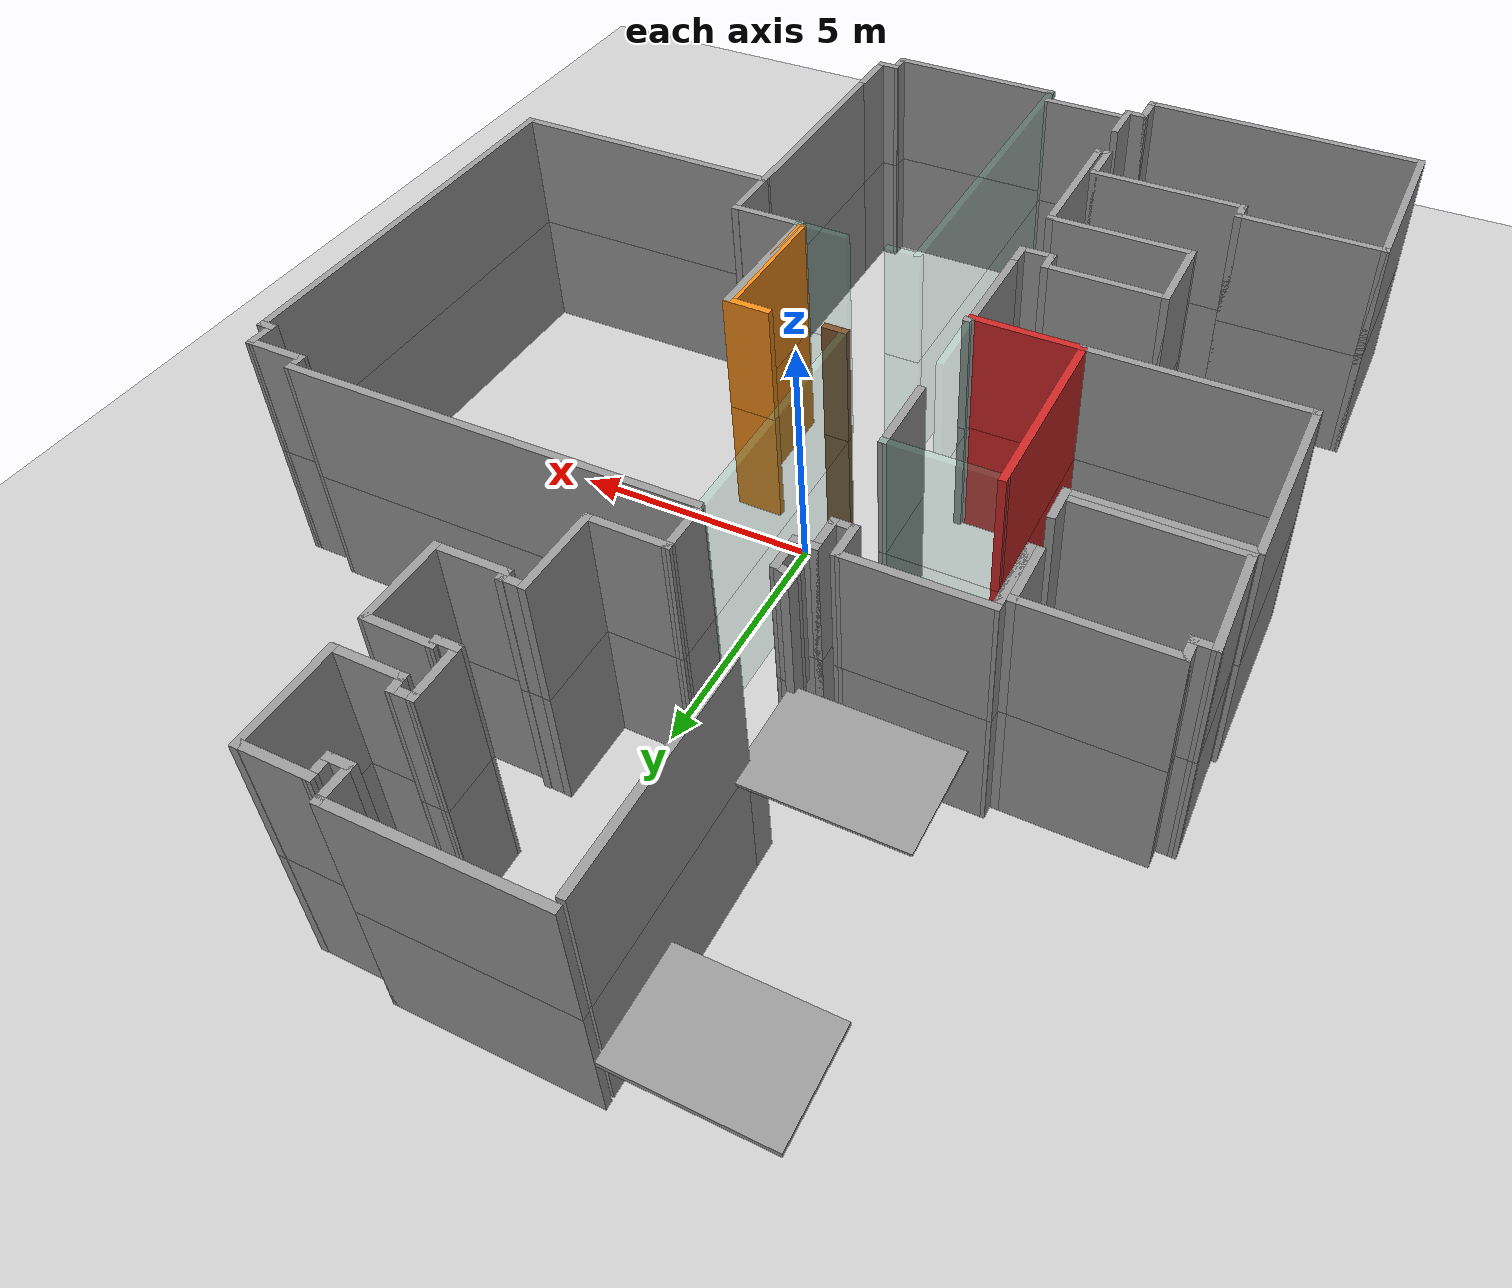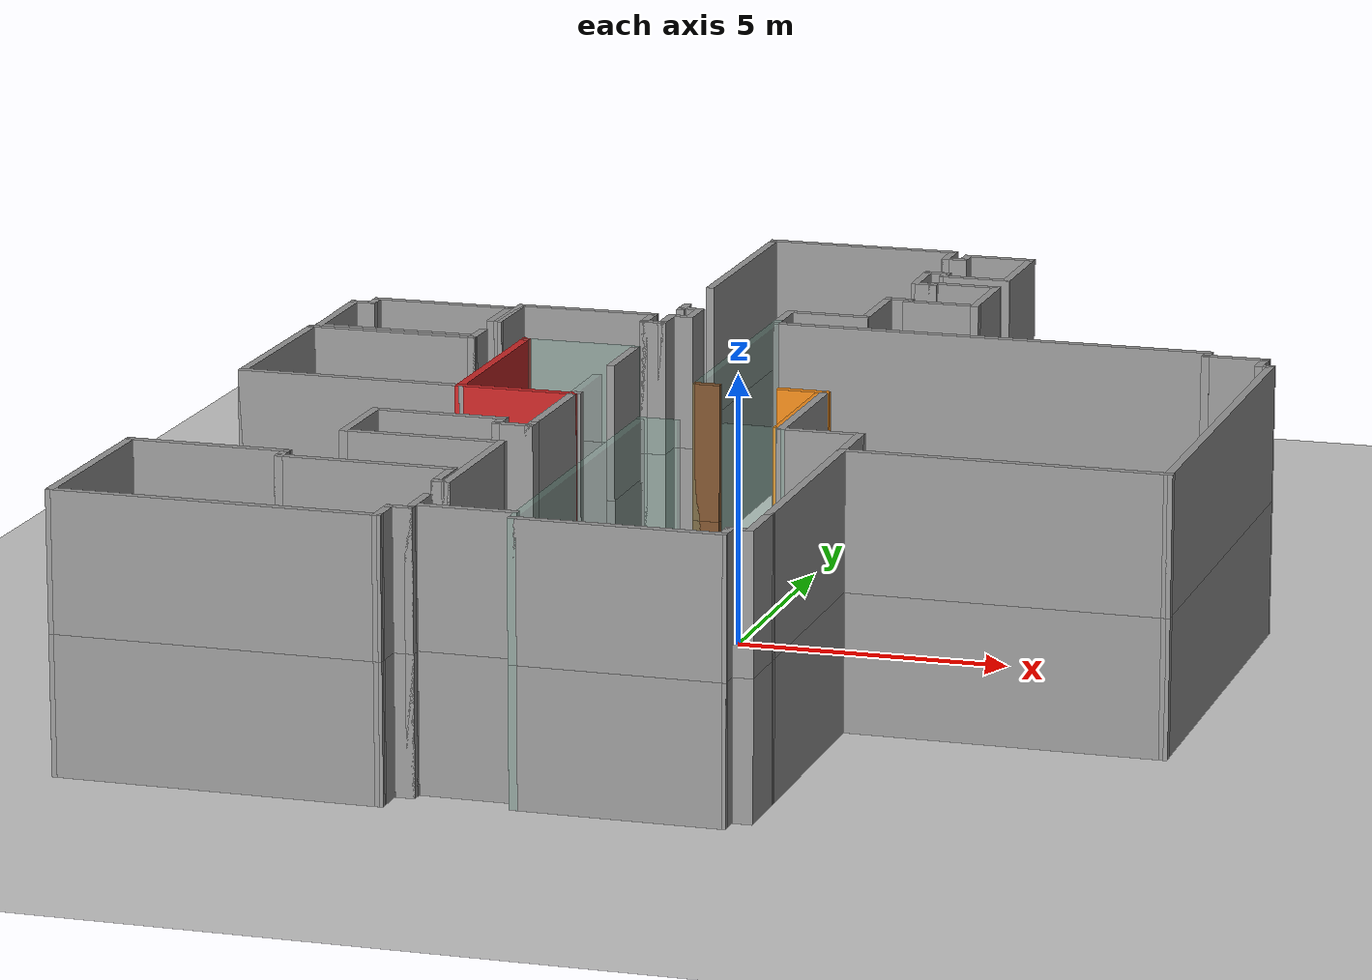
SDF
<sdf version="1.6">
 <world name="default">
  <light name="sun" type="directional"><cast_shadows>0</cast_shadows><pose>0 0 10 0 -0 0</pose></light>
  <model name="ground_plane">
   <static>1</static>
   <link name="link">
    <collision name="collision">
     <geometry><plane><normal>0 0 1</normal><size>100 100</size></plane></geometry>
     <surface><friction><ode><mu>100</mu><mu2>50</mu2></ode></friction></surface>
    </collision>
    <visual name="visual">
     <cast_shadows>0</cast_shadows>
     <geometry><plane><normal>0 0 1</normal><size>100 100</size></plane></geometry>
     <material>
      <script><uri>file://media/materials/scripts/gazebo.material</uri><name>Gazebo/Grey</name></script>
     </material>
    </visual>
   </link>
  </model>
  <gravity>0 0 -9.8</gravity>
  <magnetic_field>6e-06 2.3e-05 -4.2e-05</magnetic_field>
  <atmosphere type="adiabatic"/>
  <physics name="default_physics" default="0" type="ode">
   <max_step_size>0.001</max_step_size>
   <real_time_factor>1</real_time_factor>
   <real_time_update_rate>1000</real_time_update_rate>
  </physics>
  <scene><shadows>0</shadows></scene>
  <spherical_coordinates>
   <surface_model>EARTH_WGS84</surface_model>
   <latitude_deg>0</latitude_deg>
   <longitude_deg>0</longitude_deg>
   <elevation>0</elevation>
   <heading_deg>0</heading_deg>
  </spherical_coordinates>
  <model name="SS_office_try_2">
   <pose>0.153592 -0.122335 0 0 -0 0</pose>
   <link name="Wall_0">
    <collision name="Wall_0_Collision">
     <geometry><box><size>5.91251 0.15 2.5</size></box></geometry>
     <pose>0 0 1.25 0 -0 0</pose>
    </collision>
    <visual name="Wall_0_Visual">
     <pose>0 0 1.25 0 -0 0</pose>
     <geometry><box><size>5.91251 0.15 2.5</size></box></geometry>
     <material>
      <script><uri>file://media/materials/scripts/gazebo.material</uri><name>Gazebo/Grey</name></script>
      <ambient>1 1 1 1</ambient>
     </material>
     <meta><layer>0</layer></meta>
    </visual>
    <pose>-5.91425 -11.0474 0 0 -0 3.13893</pose>
   </link>
   <link name="Wall_1">
    <collision name="Wall_1_Collision">
     <geometry><box><size>3.75 0.15 2.5</size></box></geometry>
     <pose>0 0 1.25 0 -0 0</pose>
    </collision>
    <visual name="Wall_1_Visual">
     <pose>0 0 1.25 0 -0 0</pose>
     <geometry><box><size>3.75 0.15 2.5</size></box></geometry>
     <material>
      <script><uri>file://media/materials/scripts/gazebo.material</uri><name>Gazebo/Grey</name></script>
      <ambient>1 1 1 1</ambient>
     </material>
     <meta><layer>0</layer></meta>
    </visual>
    <pose>-8.79549 -9.23977 0 0 -0 1.5708</pose>
   </link>
   <link name="Wall_10">
    <collision name="Wall_10_Collision">
     <geometry><box><size>1.75 0.15 2.5</size></box></geometry>
     <pose>0 0 1.25 0 -0 0</pose>
    </collision>
    <visual name="Wall_10_Visual">
     <pose>0 0 1.25 0 -0 0</pose>
     <geometry><box><size>1.75 0.15 2.5</size></box></geometry>
     <material>
      <script><uri>file://media/materials/scripts/gazebo.material</uri><name>Gazebo/Grey</name></script>
      <ambient>1 1 1 1</ambient>
     </material>
     <meta><layer>0</layer></meta>
    </visual>
    <pose>-5.49549 -4.98977 0 0 -0 1.5708</pose>
   </link>
   <link name="Wall_100">
    <collision name="Wall_100_Collision">
     <geometry><box><size>0.379823 0.15 2.5</size></box></geometry>
     <pose>0 0 1.25 0 -0 0</pose>
    </collision>
    <visual name="Wall_100_Visual">
     <pose>0 0 1.25 0 -0 0</pose>
     <geometry><box><size>0.379823 0.15 2.5</size></box></geometry>
     <material>
      <script><uri>file://media/materials/scripts/gazebo.material</uri><name>Gazebo/Grey</name></script>
      <ambient>1 1 1 1</ambient>
     </material>
     <meta><layer>0</layer></meta>
    </visual>
    <pose>1.28072 9.07016 0 0 -0 1.63617</pose>
   </link>
   <link name="Wall_101">
    <collision name="Wall_101_Collision">
     <geometry><box><size>0.5 0.15 2.5</size></box></geometry>
     <pose>0 0 1.25 0 -0 0</pose>
    </collision>
    <visual name="Wall_101_Visual">
     <pose>0 0 1.25 0 -0 0</pose>
     <geometry><box><size>0.5 0.15 2.5</size></box></geometry>
     <material>
      <script><uri>file://media/materials/scripts/gazebo.material</uri><name>Gazebo/Grey</name></script>
      <ambient>1 1 1 1</ambient>
     </material>
     <meta><layer>0</layer></meta>
    </visual>
    <pose>1.10572 9.18501 0 0 -0 3.14159</pose>
   </link>
   <link name="Wall_102">
    <collision name="Wall_102_Collision">
     <geometry><box><size>1.12973 0.15 2.5</size></box></geometry>
     <pose>0 0 1.25 0 -0 0</pose>
    </collision>
    <visual name="Wall_102_Visual">
     <pose>0 0 1.25 0 -0 0</pose>
     <geometry><box><size>1.12973 0.15 2.5</size></box></geometry>
     <material>
      <script><uri>file://media/materials/scripts/gazebo.material</uri><name>Gazebo/Grey</name></script>
      <ambient>1 1 1 1</ambient>
     </material>
     <meta><layer>0</layer></meta>
    </visual>
    <pose>0.930715 8.69516 0 0 0 -1.55545</pose>
   </link>
   <link name="Wall_103">
    <collision name="Wall_103_Collision">
     <geometry><box><size>0.5 0.15 2.5</size></box></geometry>
     <pose>0 0 1.25 0 -0 0</pose>
    </collision>
    <visual name="Wall_103_Visual">
     <pose>0 0 1.25 0 -0 0</pose>
     <geometry><box><size>0.5 0.15 2.5</size></box></geometry>
     <material>
      <script><uri>file://media/materials/scripts/gazebo.material</uri><name>Gazebo/Grey</name></script>
      <ambient>1 1 1 1</ambient>
     </material>
     <meta><layer>0</layer></meta>
    </visual>
    <pose>1.11323 8.20531 0 0 -0 0</pose>
   </link>
   <link name="Wall_104">
    <collision name="Wall_104_Collision">
     <geometry><box><size>0.25 0.15 2.5</size></box></geometry>
     <pose>0 0 1.25 0 -0 0</pose>
    </collision>
    <visual name="Wall_104_Visual">
     <pose>0 0 1.25 0 -0 0</pose>
     <geometry><box><size>0.25 0.15 2.5</size></box></geometry>
     <material>
      <script><uri>file://media/materials/scripts/gazebo.material</uri><name>Gazebo/Grey</name></script>
      <ambient>1 1 1 1</ambient>
     </material>
     <meta><layer>0</layer></meta>
    </visual>
    <pose>1.28823 8.25531 0 0 -0 1.5708</pose>
   </link>
   <link name="Wall_105">
    <collision name="Wall_105_Collision">
     <geometry><box><size>1.3554 0.15 2.5</size></box></geometry>
     <pose>0 0 1.25 0 -0 0</pose>
    </collision>
    <visual name="Wall_105_Visual">
     <pose>0 0 1.25 0 -0 0</pose>
     <geometry><box><size>1.3554 0.15 2.5</size></box></geometry>
     <material>
      <script><uri>file://media/materials/scripts/gazebo.material</uri><name>Gazebo/Grey</name></script>
      <ambient>1 1 1 1</ambient>
     </material>
     <meta><layer>0</layer></meta>
    </visual>
    <pose>1.89089 8.29779 0 0 0 -0.012475</pose>
   </link>
   <link name="Wall_106">
    <collision name="Wall_106_Collision">
     <geometry><box><size>1.75 0.15 2.5</size></box></geometry>
     <pose>0 0 1.25 0 -0 0</pose>
    </collision>
    <visual name="Wall_106_Visual">
     <pose>0 0 1.25 0 -0 0</pose>
     <geometry><box><size>1.75 0.15 2.5</size></box></geometry>
     <material>
      <script><uri>file://media/materials/scripts/gazebo.material</uri><name>Gazebo/Grey</name></script>
      <ambient>1 1 1 1</ambient>
     </material>
     <meta><layer>0</layer></meta>
    </visual>
    <pose>2.49354 7.49027 0 0 0 -1.5708</pose>
   </link>
   <link name="Wall_107">
    <collision name="Wall_107_Collision">
     <geometry><box><size>1.45874 0.15 2.5</size></box></geometry>
     <pose>0 0 1.25 0 -0 0</pose>
    </collision>
    <visual name="Wall_107_Visual">
     <pose>0 0 1.25 0 -0 0</pose>
     <geometry><box><size>1.45874 0.15 2.5</size></box></geometry>
     <material>
      <script><uri>file://media/materials/scripts/gazebo.material</uri><name>Gazebo/Grey</name></script>
      <ambient>1 1 1 1</ambient>
     </material>
     <meta><layer>0</layer></meta>
    </visual>
    <pose>1.84486 6.69027 0 0 -0 3.14159</pose>
   </link>
   <link name="Wall_108">
    <collision name="Wall_108_Collision">
     <geometry><box><size>0.266919 0.15 2.5</size></box></geometry>
     <pose>0 0 1.25 0 -0 0</pose>
    </collision>
    <visual name="Wall_108_Visual">
     <pose>0 0 1.25 0 -0 0</pose>
     <geometry><box><size>0.266919 0.15 2.5</size></box></geometry>
     <material>
      <script><uri>file://media/materials/scripts/gazebo.material</uri><name>Gazebo/Grey</name></script>
      <ambient>1 1 1 1</ambient>
     </material>
     <meta><layer>0</layer></meta>
    </visual>
    <pose>1.19801 6.75625 0 0 -0 1.5708</pose>
   </link>
   <link name="Wall_109">
    <collision name="Wall_109_Collision">
     <geometry><box><size>0.552631 0.15 2.5</size></box></geometry>
     <pose>0 0 1.25 0 -0 0</pose>
    </collision>
    <visual name="Wall_109_Visual">
     <pose>0 0 1.25 0 -0 0</pose>
     <geometry><box><size>0.552631 0.15 2.5</size></box></geometry>
     <material>
      <script><uri>file://media/materials/scripts/gazebo.material</uri><name>Gazebo/Grey</name></script>
      <ambient>1 1 1 1</ambient>
     </material>
     <meta><layer>0</layer></meta>
    </visual>
    <pose>1.00421 6.80719 0 0 -0 3.14159</pose>
   </link>
   <link name="Wall_11">
    <collision name="Wall_11_Collision">
     <geometry><box><size>2.5 0.15 2.5</size></box></geometry>
     <pose>0 0 1.25 0 -0 0</pose>
    </collision>
    <visual name="Wall_11_Visual">
     <pose>0 0 1.25 0 -0 0</pose>
     <geometry><box><size>2.5 0.15 2.5</size></box></geometry>
     <material>
      <script><uri>file://media/materials/scripts/gazebo.material</uri><name>Gazebo/Grey</name></script>
      <ambient>1 1 1 1</ambient>
     </material>
     <meta><layer>0</layer></meta>
    </visual>
    <pose>-4.32049 -4.18977 0 0 -0 0</pose>
   </link>
   <link name="Wall_110">
    <collision name="Wall_110_Collision">
     <geometry><box><size>1.75942 0.15 2.5</size></box></geometry>
     <pose>0 0 1.25 0 -0 0</pose>
    </collision>
    <visual name="Wall_110_Visual">
     <pose>0 0 1.25 0 -0 0</pose>
     <geometry><box><size>1.75942 0.15 2.5</size></box></geometry>
     <material>
      <script><uri>file://media/materials/scripts/gazebo.material</uri><name>Gazebo/Grey</name></script>
      <ambient>1 1 1 1</ambient>
     </material>
     <meta><layer>0</layer></meta>
    </visual>
    <pose>0.791618 6.01001 0 0 0 -1.57547</pose>
   </link>
   <link name="Wall_111">
    <collision name="Wall_111_Collision">
     <geometry><box><size>1.59211 0.15 2.5</size></box></geometry>
     <pose>0 0 1.25 0 -0 0</pose>
    </collision>
    <visual name="Wall_111_Visual">
     <pose>0 0 1.25 0 -0 0</pose>
     <geometry><box><size>1.59211 0.15 2.5</size></box></geometry>
     <material>
      <script><uri>file://media/materials/scripts/gazebo.material</uri><name>Gazebo/Grey</name></script>
      <ambient>1 1 1 1</ambient>
     </material>
     <meta><layer>0</layer></meta>
    </visual>
    <pose>0.059287 5.20155 0 0 -0 3.13638</pose>
   </link>
   <link name="Wall_113">
    <collision name="Wall_113_Collision">
     <geometry><box><size>1 0.15 2.5</size></box></geometry>
     <pose>0 0 1.25 0 -0 0</pose>
    </collision>
    <visual name="Wall_113_Visual">
     <pose>0 0 1.25 0 -0 0</pose>
     <geometry><box><size>1 0.15 2.5</size></box></geometry>
     <material>
      <script><uri>file://media/materials/scripts/gazebo.material</uri><name>Gazebo/Grey</name></script>
      <ambient>1 1 1 1</ambient>
     </material>
     <meta><layer>0</layer></meta>
    </visual>
    <pose>-0.661766 4.78031 0 0 0 -1.5708</pose>
   </link>
   <link name="Wall_115">
    <collision name="Wall_115_Collision">
     <geometry><box><size>5.25 0.15 2.5</size></box></geometry>
     <pose>0 0 1.25 0 -0 0</pose>
    </collision>
    <visual name="Wall_115_Visual">
     <pose>0 0 1.25 0 -0 0</pose>
     <geometry><box><size>5.25 0.15 2.5</size></box></geometry>
     <material>
      <script><uri>file://media/materials/scripts/gazebo.material</uri><name>Gazebo/Grey</name></script>
      <ambient>0.435 0.796 0.675 1</ambient>
      <diffuse>0.7 0.7 0.7 1</diffuse>
      <specular>0.01 0.01 0.01 1</specular>
      <emissive>0 0 0 1</emissive>
     </material>
     <meta><layer>0</layer></meta>
     <transparency>0.8</transparency>
    </visual>
    <pose>-0.661766 1.80531 0 0 0 -1.5708</pose>
   </link>
   <link name="Wall_116">
    <collision name="Wall_116_Collision">
     <geometry><box><size>0.5 0.15 2.5</size></box></geometry>
     <pose>0 0 1.25 0 -0 0</pose>
    </collision>
    <visual name="Wall_116_Visual">
     <pose>0 0 1.25 0 -0 0</pose>
     <geometry><box><size>0.5 0.15 2.5</size></box></geometry>
     <material>
      <script><uri>file://media/materials/scripts/gazebo.material</uri><name>Gazebo/Brown</name></script>
      <ambient>1 1 1 1</ambient>
     </material>
     <meta><layer>0</layer></meta>
    </visual>
    <pose>-0.486766 -0.744691 0 0 -0 0</pose>
   </link>
   <link name="Wall_118">
    <collision name="Wall_118_Collision">
     <geometry><box><size>0.961189 0.15 2.5</size></box></geometry>
     <pose>0 0 1.25 0 -0 0</pose>
    </collision>
    <visual name="Wall_118_Visual">
     <pose>0 0 1.25 0 -0 0</pose>
     <geometry><box><size>0.961189 0.15 2.5</size></box></geometry>
     <material>
      <script><uri>file://media/materials/scripts/gazebo.material</uri><name>Gazebo/Orange</name></script>
      <ambient>1 1 1 1</ambient>
     </material>
     <meta><layer>0</layer></meta>
    </visual>
    <pose>1.28357 -0.707118 0 0 0 -0.008354</pose>
   </link>
   <link name="Wall_119">
    <collision name="Wall_119_Collision">
     <geometry><box><size>2.92618 0.15 2.5</size></box></geometry>
     <pose>0 0 1.25 0 -0 0</pose>
    </collision>
    <visual name="Wall_119_Visual">
     <pose>0 0 1.25 0 -0 0</pose>
     <geometry><box><size>2.92618 0.15 2.5</size></box></geometry>
     <material>
      <script><uri>file://media/materials/scripts/gazebo.material</uri><name>Gazebo/Grey</name></script>
      <ambient>1 1 1 1</ambient>
     </material>
     <meta><layer>0</layer></meta>
    </visual>
    <pose>1.68237 -2.11215 0 0 0 -1.5708</pose>
   </link>
   <link name="Wall_12">
    <collision name="Wall_12_Collision">
     <geometry><box><size>0.5 0.15 2.5</size></box></geometry>
     <pose>0 0 1.25 0 -0 0</pose>
    </collision>
    <visual name="Wall_12_Visual">
     <pose>0 0 1.25 0 -0 0</pose>
     <geometry><box><size>0.5 0.15 2.5</size></box></geometry>
     <material>
      <script><uri>file://media/materials/scripts/gazebo.material</uri><name>Gazebo/Grey</name></script>
      <ambient>1 1 1 1</ambient>
     </material>
     <meta><layer>0</layer></meta>
    </visual>
    <pose>-3.14549 -4.36477 0 0 0 -1.5708</pose>
   </link>
   <link name="Wall_120">
    <collision name="Wall_120_Collision">
     <geometry><box><size>1.55423 0.15 2.5</size></box></geometry>
     <pose>0 0 1.25 0 -0 0</pose>
    </collision>
    <visual name="Wall_120_Visual">
     <pose>0 0 1.25 0 -0 0</pose>
     <geometry><box><size>1.55423 0.15 2.5</size></box></geometry>
     <material>
      <script><uri>file://media/materials/scripts/gazebo.material</uri><name>Gazebo/Grey</name></script>
      <ambient>1 1 1 1</ambient>
     </material>
     <meta><layer>0</layer></meta>
    </visual>
    <pose>2.39125 -3.50363 0 0 -0 0.004826</pose>
   </link>
   <link name="Wall_121">
    <collision name="Wall_121_Collision">
     <geometry><box><size>1.31028 0.15 2.5</size></box></geometry>
     <pose>0 0 1.25 0 -0 0</pose>
    </collision>
    <visual name="Wall_121_Visual">
     <pose>0 0 1.25 0 -0 0</pose>
     <geometry><box><size>1.31028 0.15 2.5</size></box></geometry>
     <material>
      <script><uri>file://media/materials/scripts/gazebo.material</uri><name>Gazebo/Grey</name></script>
      <ambient>1 1 1 1</ambient>
     </material>
     <meta><layer>0</layer></meta>
    </visual>
    <pose>3.08997 -4.0736 0 0 0 -1.56496</pose>
   </link>
   <link name="Wall_122">
    <collision name="Wall_122_Collision">
     <geometry><box><size>5.85233 0.15 2.5</size></box></geometry>
     <pose>0 0 1.25 0 -0 0</pose>
    </collision>
    <visual name="Wall_122_Visual">
     <pose>0 0 1.25 0 -0 0</pose>
     <geometry><box><size>5.85233 0.15 2.5</size></box></geometry>
     <material>
      <script><uri>file://media/materials/scripts/gazebo.material</uri><name>Gazebo/Grey</name></script>
      <ambient>1 1 1 1</ambient>
     </material>
     <meta><layer>0</layer></meta>
    </visual>
    <pose>5.94452 -4.65373 0 0 -0 0</pose>
   </link>
   <link name="Wall_123">
    <collision name="Wall_123_Collision">
     <geometry><box><size>8.28775 0.15 2.5</size></box></geometry>
     <pose>0 0 1.25 0 -0 0</pose>
    </collision>
    <visual name="Wall_123_Visual">
     <pose>0 0 1.25 0 -0 0</pose>
     <geometry><box><size>8.28775 0.15 2.5</size></box></geometry>
     <material>
      <script><uri>file://media/materials/scripts/gazebo.material</uri><name>Gazebo/Grey</name></script>
      <ambient>1 1 1 1</ambient>
     </material>
     <meta><layer>0</layer></meta>
    </visual>
    <pose>8.78622 -0.584854 0 0 -0 1.57126</pose>
   </link>
   <link name="Wall_124">
    <collision name="Wall_124_Collision">
     <geometry><box><size>0.352219 0.15 2.5</size></box></geometry>
     <pose>0 0 1.25 0 -0 0</pose>
    </collision>
    <visual name="Wall_124_Visual">
     <pose>0 0 1.25 0 -0 0</pose>
     <geometry><box><size>0.352219 0.15 2.5</size></box></geometry>
     <material>
      <script><uri>file://media/materials/scripts/gazebo.material</uri><name>Gazebo/Grey</name></script>
      <ambient>1 1 1 1</ambient>
     </material>
     <meta><layer>0</layer></meta>
    </visual>
    <pose>8.68323 3.48971 0 0 -0 3.12285</pose>
   </link>
   <link name="Wall_125">
    <collision name="Wall_125_Collision">
     <geometry><box><size>0.636677 0.15 2.5</size></box></geometry>
     <pose>0 0 1.25 0 -0 0</pose>
    </collision>
    <visual name="Wall_125_Visual">
     <pose>0 0 1.25 0 -0 0</pose>
     <geometry><box><size>0.636677 0.15 2.5</size></box></geometry>
     <material>
      <script><uri>file://media/materials/scripts/gazebo.material</uri><name>Gazebo/Grey</name></script>
      <ambient>1 1 1 1</ambient>
     </material>
     <meta><layer>0</layer></meta>
    </visual>
    <pose>8.58585 3.73103 0 0 -0 1.53995</pose>
   </link>
   <link name="Wall_126">
    <collision name="Wall_126_Collision">
     <geometry><box><size>1.25 0.15 2.5</size></box></geometry>
     <pose>0 0 1.25 0 -0 0</pose>
    </collision>
    <visual name="Wall_126_Visual">
     <pose>0 0 1.25 0 -0 0</pose>
     <geometry><box><size>1.25 0.15 2.5</size></box></geometry>
     <material>
      <script><uri>file://media/materials/scripts/gazebo.material</uri><name>Gazebo/Grey</name></script>
      <ambient>1 1 1 1</ambient>
     </material>
     <meta><layer>0</layer></meta>
    </visual>
    <pose>8.04336 3.97426 0 0 -0 3.14159</pose>
   </link>
   <link name="Wall_127">
    <collision name="Wall_127_Collision">
     <geometry><box><size>0.411283 0.15 2.5</size></box></geometry>
     <pose>0 0 1.25 0 -0 0</pose>
    </collision>
    <visual name="Wall_127_Visual">
     <pose>0 0 1.25 0 -0 0</pose>
     <geometry><box><size>0.411283 0.15 2.5</size></box></geometry>
     <material>
      <script><uri>file://media/materials/scripts/gazebo.material</uri><name>Gazebo/Grey</name></script>
      <ambient>1 1 1 1</ambient>
     </material>
     <meta><layer>0</layer></meta>
    </visual>
    <pose>7.49234 4.1011 0 0 -0 1.57861</pose>
   </link>
   <link name="Wall_128">
    <collision name="Wall_128_Collision">
     <geometry><box><size>8.25 0.15 2.5</size></box></geometry>
     <pose>0 0 1.25 0 -0 0</pose>
    </collision>
    <visual name="Wall_128_Visual">
     <pose>0 0 1.25 0 -0 0</pose>
     <geometry><box><size>8.25 0.15 2.5</size></box></geometry>
     <material>
      <script><uri>file://media/materials/scripts/gazebo.material</uri><name>Gazebo/Grey</name></script>
      <ambient>1 1 1 1</ambient>
     </material>
     <meta><layer>0</layer></meta>
    </visual>
    <pose>3.43753 4.23174 0 0 -0 3.14159</pose>
   </link>
   <link name="Wall_13">
    <collision name="Wall_13_Collision">
     <geometry><box><size>0.75 0.15 2.5</size></box></geometry>
     <pose>0 0 1.25 0 -0 0</pose>
    </collision>
    <visual name="Wall_13_Visual">
     <pose>0 0 1.25 0 -0 0</pose>
     <geometry><box><size>0.75 0.15 2.5</size></box></geometry>
     <material>
      <script><uri>file://media/materials/scripts/gazebo.material</uri><name>Gazebo/Grey</name></script>
      <ambient>1 1 1 1</ambient>
     </material>
     <meta><layer>0</layer></meta>
    </visual>
    <pose>-2.84549 -4.53977 0 0 -0 0</pose>
   </link>
   <link name="Wall_134">
    <collision name="Wall_134_Collision">
     <geometry><box><size>1.13806 0.15 2.5</size></box></geometry>
     <pose>0 0 1.25 0 -0 0</pose>
    </collision>
    <visual name="Wall_134_Visual">
     <pose>0 0 1.25 0 -0 0</pose>
     <geometry><box><size>1.13806 0.15 2.5</size></box></geometry>
     <material>
      <script><uri>file://media/materials/scripts/gazebo.material</uri><name>Gazebo/Grey</name></script>
      <ambient>0.435 0.796 0.675 1</ambient>
      <diffuse>0.7 0.7 0.7 1</diffuse>
      <specular>0.01 0.01 0.01 1</specular>
      <emissive>0 0 0 1</emissive>
     </material>
     <meta><layer>0</layer></meta>
     <transparency>0.8</transparency>
    </visual>
    <pose>1.19527 -3.49491 0 0 0 -0.024517</pose>
   </link>
   <link name="Wall_136">
    <collision name="Wall_136_Collision">
     <geometry><box><size>2.75 0.15 2.5</size></box></geometry>
     <pose>0 0 1.25 0 -0 0</pose>
    </collision>
    <visual name="Wall_136_Visual">
     <pose>0 0 1.25 0 -0 0</pose>
     <geometry><box><size>2.75 0.15 2.5</size></box></geometry>
     <material>
      <script><uri>file://media/materials/scripts/gazebo.material</uri><name>Gazebo/Orange</name></script>
      <ambient>1 1 1 1</ambient>
     </material>
     <meta><layer>0</layer></meta>
    </visual>
    <pose>1.60652 -2.11221 0 0 0 -1.5708</pose>
   </link>
   <link name="Wall_138">
    <collision name="Wall_138_Collision">
     <geometry><box><size>0.75 0.15 2.5</size></box></geometry>
     <pose>0 0 1.25 0 -0 0</pose>
    </collision>
    <visual name="Wall_138_Visual">
     <pose>0 0 1.25 0 -0 0</pose>
     <geometry><box><size>0.75 0.15 2.5</size></box></geometry>
     <material>
      <script><uri>file://media/materials/scripts/gazebo.material</uri><name>Gazebo/Grey</name></script>
      <ambient>0.435 0.796 0.675 1</ambient>
      <diffuse>0.7 0.7 0.7 1</diffuse>
      <specular>0.01 0.01 0.01 1</specular>
      <emissive>0 0 0 1</emissive>
     </material>
     <meta><layer>0</layer></meta>
     <transparency>0.8</transparency>
    </visual>
    <pose>-0.548157 -3.49201 0 0 -0 3.14159</pose>
   </link>
   <link name="Wall_139">
    <collision name="Wall_139_Collision">
     <geometry><box><size>7.25 0.15 2.5</size></box></geometry>
     <pose>0 0 1.25 0 -0 0</pose>
    </collision>
    <visual name="Wall_139_Visual">
     <pose>0 0 1.25 0 -0 0</pose>
     <geometry><box><size>7.25 0.15 2.5</size></box></geometry>
     <material>
      <script><uri>file://media/materials/scripts/gazebo.material</uri><name>Gazebo/Grey</name></script>
      <ambient>0.435 0.796 0.675 1</ambient>
      <diffuse>0.7 0.7 0.7 1</diffuse>
      <specular>0.01 0.01 0.01 1</specular>
      <emissive>0 0 0 1</emissive>
     </material>
     <meta><layer>0</layer></meta>
     <transparency>0.8</transparency>
    </visual>
    <pose>-0.848157 -7.04201 0 0 0 -1.5708</pose>
   </link>
   <link name="Wall_141">
    <collision name="Wall_141_Collision">
     <geometry><box><size>3.75 0.15 2.5</size></box></geometry>
     <pose>0 0 1.25 0 -0 0</pose>
    </collision>
    <visual name="Wall_141_Visual">
     <pose>0 0 1.25 0 -0 0</pose>
     <geometry><box><size>3.75 0.15 2.5</size></box></geometry>
     <material>
      <script><uri>file://media/materials/scripts/gazebo.material</uri><name>Gazebo/Grey</name></script>
      <ambient>1 1 1 1</ambient>
     </material>
     <meta><layer>0</layer></meta>
    </visual>
    <pose>0.951844 -10.592 0 0 -0 0</pose>
   </link>
   <link name="Wall_142">
    <collision name="Wall_142_Collision">
     <geometry><box><size>0.520329 0.15 2.5</size></box></geometry>
     <pose>0 0 1.25 0 -0 0</pose>
    </collision>
    <visual name="Wall_142_Visual">
     <pose>0 0 1.25 0 -0 0</pose>
     <geometry><box><size>0.520329 0.15 2.5</size></box></geometry>
     <material>
      <script><uri>file://media/materials/scripts/gazebo.material</uri><name>Gazebo/Grey</name></script>
      <ambient>1 1 1 1</ambient>
     </material>
     <meta><layer>0</layer></meta>
    </visual>
    <pose>2.75354 -10.4068 0 0 -0 1.56165</pose>
   </link>
   <link name="Wall_145">
    <collision name="Wall_145_Collision">
     <geometry><box><size>0.5 0.15 2.5</size></box></geometry>
     <pose>0 0 1.25 0 -0 0</pose>
    </collision>
    <visual name="Wall_145_Visual">
     <pose>0 0 1.25 0 -0 0</pose>
     <geometry><box><size>0.5 0.15 2.5</size></box></geometry>
     <material>
      <script><uri>file://media/materials/scripts/gazebo.material</uri><name>Gazebo/Grey</name></script>
      <ambient>1 1 1 1</ambient>
     </material>
     <meta><layer>0</layer></meta>
    </visual>
    <pose>2.93023 -10.2217 0 0 -0 0</pose>
   </link>
   <link name="Wall_146">
    <collision name="Wall_146_Collision">
     <geometry><box><size>1.25 0.15 2.5</size></box></geometry>
     <pose>0 0 1.25 0 -0 0</pose>
    </collision>
    <visual name="Wall_146_Visual">
     <pose>0 0 1.25 0 -0 0</pose>
     <geometry><box><size>1.25 0.15 2.5</size></box></geometry>
     <material>
      <script><uri>file://media/materials/scripts/gazebo.material</uri><name>Gazebo/Grey</name></script>
      <ambient>1 1 1 1</ambient>
     </material>
     <meta><layer>0</layer></meta>
    </visual>
    <pose>3.10523 -9.67168 0 0 -0 1.5708</pose>
   </link>
   <link name="Wall_147">
    <collision name="Wall_147_Collision">
     <geometry><box><size>4.61797 0.15 2.5</size></box></geometry>
     <pose>0 0 1.25 0 -0 0</pose>
    </collision>
    <visual name="Wall_147_Visual">
     <pose>0 0 1.25 0 -0 0</pose>
     <geometry><box><size>4.61797 0.15 2.5</size></box></geometry>
     <material>
      <script><uri>file://media/materials/scripts/gazebo.material</uri><name>Gazebo/Grey</name></script>
      <ambient>1 1 1 1</ambient>
     </material>
     <meta><layer>0</layer></meta>
    </visual>
    <pose>3.0993 -6.88771 0 0 -0 1.57345</pose>
   </link>
   <link name="Wall_149">
    <collision name="Wall_149_Collision">
     <geometry><box><size>1.75 0.15 2.5</size></box></geometry>
     <pose>0 0 1.25 0 -0 0</pose>
    </collision>
    <visual name="Wall_149_Visual">
     <pose>0 0 1.25 0 -0 0</pose>
     <geometry><box><size>1.75 0.15 2.5</size></box></geometry>
     <material>
      <script><uri>file://media/materials/scripts/gazebo.material</uri><name>Gazebo/Grey</name></script>
      <ambient>1 1 1 1</ambient>
     </material>
     <meta><layer>0</layer></meta>
    </visual>
    <pose>-1.74079 -10.2333 0 0 -0 3.14159</pose>
   </link>
   <link name="Wall_151">
    <collision name="Wall_151_Collision">
     <geometry><box><size>1 0.15 2.5</size></box></geometry>
     <pose>0 0 1.25 0 -0 0</pose>
    </collision>
    <visual name="Wall_151_Visual">
     <pose>0 0 1.25 0 -0 0</pose>
     <geometry><box><size>1 0.15 2.5</size></box></geometry>
     <material>
      <script><uri>file://media/materials/scripts/gazebo.material</uri><name>Gazebo/Grey</name></script>
      <ambient>1 1 1 1</ambient>
     </material>
     <meta><layer>0</layer></meta>
    </visual>
    <pose>-2.68301 -10.0301 0 0 0 -1.5708</pose>
   </link>
   <link name="Wall_152">
    <collision name="Wall_152_Collision">
     <geometry><box><size>0.5 0.15 2.5</size></box></geometry>
     <pose>0 0 1.25 0 -0 0</pose>
    </collision>
    <visual name="Wall_152_Visual">
     <pose>0 0 1.25 0 -0 0</pose>
     <geometry><box><size>0.5 0.15 2.5</size></box></geometry>
     <material>
      <script><uri>file://media/materials/scripts/gazebo.material</uri><name>Gazebo/Grey</name></script>
      <ambient>1 1 1 1</ambient>
     </material>
     <meta><layer>0</layer></meta>
    </visual>
    <pose>-2.85801 -10.4551 0 0 -0 3.14159</pose>
   </link>
   <link name="Wall_153">
    <collision name="Wall_153_Collision">
     <geometry><box><size>0.75 0.15 2.5</size></box></geometry>
     <pose>0 0 1.25 0 -0 0</pose>
    </collision>
    <visual name="Wall_153_Visual">
     <pose>0 0 1.25 0 -0 0</pose>
     <geometry><box><size>0.75 0.15 2.5</size></box></geometry>
     <material>
      <script><uri>file://media/materials/scripts/gazebo.material</uri><name>Gazebo/Grey</name></script>
      <ambient>1 1 1 1</ambient>
     </material>
     <meta><layer>0</layer></meta>
    </visual>
    <pose>-3.03301 -10.7551 0 0 0 -1.5708</pose>
   </link>
   <link name="Wall_155">
    <collision name="Wall_155_Collision">
     <geometry><box><size>1.62091 0.15 2.5</size></box></geometry>
     <pose>0 0 1.25 0 -0 0</pose>
    </collision>
    <visual name="Wall_155_Visual">
     <pose>0 0 1.25 0 -0 0</pose>
     <geometry><box><size>1.62091 0.15 2.5</size></box></geometry>
     <material>
      <script><uri>file://media/materials/scripts/gazebo.material</uri><name>Gazebo/Grey</name></script>
      <ambient>1 1 1 1</ambient>
     </material>
     <meta><layer>0</layer></meta>
    </visual>
    <pose>-2.55275 0.898318 0 0 -0 1.57861</pose>
   </link>
   <link name="Wall_2">
    <collision name="Wall_2_Collision">
     <geometry><box><size>3 0.15 2.5</size></box></geometry>
     <pose>0 0 1.25 0 -0 0</pose>
    </collision>
    <visual name="Wall_2_Visual">
     <pose>0 0 1.25 0 -0 0</pose>
     <geometry><box><size>3 0.15 2.5</size></box></geometry>
     <material>
      <script><uri>file://media/materials/scripts/gazebo.material</uri><name>Gazebo/Grey</name></script>
      <ambient>1 1 1 1</ambient>
     </material>
     <meta><layer>0</layer></meta>
    </visual>
    <pose>-7.37049 -7.43977 0 0 -0 0</pose>
   </link>
   <link name="Wall_28">
    <collision name="Wall_28_Collision">
     <geometry><box><size>0.15 0.15 2.5</size></box></geometry>
     <pose>0 0 1.25 0 -0 0</pose>
    </collision>
    <visual name="Wall_28_Visual">
     <pose>0 0 1.25 0 -0 0</pose>
     <geometry><box><size>0.15 0.15 2.5</size></box></geometry>
     <material>
      <script><uri>file://media/materials/scripts/gazebo.material</uri><name>Gazebo/Grey</name></script>
      <ambient>1 1 1 1</ambient>
     </material>
     <meta><layer>0</layer></meta>
    </visual>
    <pose>-2.48781 -2.00969 0 0 -0 0</pose>
   </link>
   <link name="Wall_3">
    <collision name="Wall_3_Collision">
     <geometry><box><size>0.5 0.15 2.5</size></box></geometry>
     <pose>0 0 1.25 0 -0 0</pose>
    </collision>
    <visual name="Wall_3_Visual">
     <pose>0 0 1.25 0 -0 0</pose>
     <geometry><box><size>0.5 0.15 2.5</size></box></geometry>
     <material>
      <script><uri>file://media/materials/scripts/gazebo.material</uri><name>Gazebo/Grey</name></script>
      <ambient>1 1 1 1</ambient>
     </material>
     <meta><layer>0</layer></meta>
    </visual>
    <pose>-5.94549 -7.61477 0 0 0 -1.5708</pose>
   </link>
   <link name="Wall_39">
    <collision name="Wall_39_Collision">
     <geometry><box><size>0.5 0.15 2.5</size></box></geometry>
     <pose>0 0 1.25 0 -0 0</pose>
    </collision>
    <visual name="Wall_39_Visual">
     <pose>0 0 1.25 0 -0 0</pose>
     <geometry><box><size>0.5 0.15 2.5</size></box></geometry>
     <material>
      <script><uri>file://media/materials/scripts/gazebo.material</uri><name>Gazebo/Grey</name></script>
      <ambient>1 1 1 1</ambient>
     </material>
     <meta><layer>0</layer></meta>
    </visual>
    <pose>-2.54549 -4.36477 0 0 -0 1.5708</pose>
   </link>
   <link name="Wall_4">
    <collision name="Wall_4_Collision">
     <geometry><box><size>3.25 0.15 2.5</size></box></geometry>
     <pose>0 0 1.25 0 -0 0</pose>
    </collision>
    <visual name="Wall_4_Visual">
     <pose>0 0 1.25 0 -0 0</pose>
     <geometry><box><size>3.25 0.15 2.5</size></box></geometry>
     <material>
      <script><uri>file://media/materials/scripts/gazebo.material</uri><name>Gazebo/Grey</name></script>
      <ambient>1 1 1 1</ambient>
     </material>
     <meta><layer>0</layer></meta>
    </visual>
    <pose>-4.39549 -7.78977 0 0 -0 0</pose>
   </link>
   <link name="Wall_40">
    <collision name="Wall_40_Collision">
     <geometry><box><size>2.25 0.15 2.5</size></box></geometry>
     <pose>0 0 1.25 0 -0 0</pose>
    </collision>
    <visual name="Wall_40_Visual">
     <pose>0 0 1.25 0 -0 0</pose>
     <geometry><box><size>2.25 0.15 2.5</size></box></geometry>
     <material>
      <script><uri>file://media/materials/scripts/gazebo.material</uri><name>Gazebo/Grey</name></script>
      <ambient>1 1 1 1</ambient>
     </material>
     <meta><layer>0</layer></meta>
    </visual>
    <pose>-2.54549 -3.13977 0 0 -0 1.5708</pose>
   </link>
   <link name="Wall_42">
    <collision name="Wall_42_Collision">
     <geometry><box><size>1.56365 0.15 2.5</size></box></geometry>
     <pose>0 0 1.25 0 -0 0</pose>
    </collision>
    <visual name="Wall_42_Visual">
     <pose>0 0 1.25 0 -0 0</pose>
     <geometry><box><size>1.56365 0.15 2.5</size></box></geometry>
     <material>
      <script><uri>file://media/materials/scripts/gazebo.material</uri><name>Gazebo/Grey</name></script>
      <ambient>0.435 0.796 0.675 1</ambient>
      <diffuse>0.7 0.7 0.7 1</diffuse>
      <specular>0.01 0.01 0.01 1</specular>
      <emissive>0 0 0 1</emissive>
     </material>
     <meta><layer>0</layer></meta>
     <transparency>0.8</transparency>
    </visual>
    <pose>-2.55627 -1.38303 0 0 0 -1.55555</pose>
   </link>
   <link name="Wall_43">
    <collision name="Wall_43_Collision">
     <geometry><box><size>2.25 0.15 2.5</size></box></geometry>
     <pose>0 0 1.25 0 -0 0</pose>
    </collision>
    <visual name="Wall_43_Visual">
     <pose>0 0 1.25 0 -0 0</pose>
     <geometry><box><size>2.25 0.15 2.5</size></box></geometry>
     <material>
      <script><uri>file://media/materials/scripts/gazebo.material</uri><name>Gazebo/Red</name></script>
      <ambient>1 1 1 1</ambient>
     </material>
     <meta><layer>0</layer></meta>
    </visual>
    <pose>-3.59549 -2.08977 0 0 -0 3.14159</pose>
   </link>
   <link name="Wall_45">
    <collision name="Wall_45_Collision">
     <geometry><box><size>3.88655 0.15 2.5</size></box></geometry>
     <pose>0 0 1.25 0 -0 0</pose>
    </collision>
    <visual name="Wall_45_Visual">
     <pose>0 0 1.25 0 -0 0</pose>
     <geometry><box><size>3.88655 0.15 2.5</size></box></geometry>
     <material>
      <script><uri>file://media/materials/scripts/gazebo.material</uri><name>Gazebo/Red</name></script>
      <ambient>1 1 1 1</ambient>
     </material>
     <meta><layer>0</layer></meta>
    </visual>
    <pose>-4.65199 -0.221511 0 0 -0 1.57428</pose>
   </link>
   <link name="Wall_47">
    <collision name="Wall_47_Collision">
     <geometry><box><size>2.25 0.15 2.5</size></box></geometry>
     <pose>0 0 1.25 0 -0 0</pose>
    </collision>
    <visual name="Wall_47_Visual">
     <pose>0 0 1.25 0 -0 0</pose>
     <geometry><box><size>2.25 0.15 2.5</size></box></geometry>
     <material>
      <script><uri>file://media/materials/scripts/gazebo.material</uri><name>Gazebo/Grey</name></script>
      <ambient>0.435 0.796 0.675 1</ambient>
      <diffuse>0.7 0.7 0.7 1</diffuse>
      <specular>0.01 0.01 0.01 1</specular>
      <emissive>0 0 0 1</emissive>
     </material>
     <meta><layer>0</layer></meta>
     <transparency>0.8</transparency>
    </visual>
    <pose>-3.6085 1.63375 0 0 -0 0</pose>
   </link>
   <link name="Wall_49">
    <collision name="Wall_49_Collision">
     <geometry><box><size>4.25 0.15 2.5</size></box></geometry>
     <pose>0 0 1.25 0 -0 0</pose>
    </collision>
    <visual name="Wall_49_Visual">
     <pose>0 0 1.25 0 -0 0</pose>
     <geometry><box><size>4.25 0.15 2.5</size></box></geometry>
     <material>
      <script><uri>file://media/materials/scripts/gazebo.material</uri><name>Gazebo/Grey</name></script>
      <ambient>1 1 1 1</ambient>
     </material>
     <meta><layer>0</layer></meta>
    </visual>
    <pose>-6.69549 -2.08977 0 0 -0 3.14159</pose>
   </link>
   <link name="Wall_5">
    <collision name="Wall_5_Collision">
     <geometry><box><size>1 0.15 2.5</size></box></geometry>
     <pose>0 0 1.25 0 -0 0</pose>
    </collision>
    <visual name="Wall_5_Visual">
     <pose>0 0 1.25 0 -0 0</pose>
     <geometry><box><size>1 0.15 2.5</size></box></geometry>
     <material>
      <script><uri>file://media/materials/scripts/gazebo.material</uri><name>Gazebo/Grey</name></script>
      <ambient>1 1 1 1</ambient>
     </material>
     <meta><layer>0</layer></meta>
    </visual>
    <pose>-2.84549 -8.21477 0 0 0 -1.5708</pose>
   </link>
   <link name="Wall_51">
    <collision name="Wall_51_Collision">
     <geometry><box><size>3.75 0.15 2.5</size></box></geometry>
     <pose>0 0 1.25 0 -0 0</pose>
    </collision>
    <visual name="Wall_51_Visual">
     <pose>0 0 1.25 0 -0 0</pose>
     <geometry><box><size>3.75 0.15 2.5</size></box></geometry>
     <material>
      <script><uri>file://media/materials/scripts/gazebo.material</uri><name>Gazebo/Grey</name></script>
      <ambient>1 1 1 1</ambient>
     </material>
     <meta><layer>0</layer></meta>
    </visual>
    <pose>-8.74549 -0.289773 0 0 -0 1.5708</pose>
   </link>
   <link name="Wall_53">
    <collision name="Wall_53_Collision">
     <geometry><box><size>3.25 0.15 2.5</size></box></geometry>
     <pose>0 0 1.25 0 -0 0</pose>
    </collision>
    <visual name="Wall_53_Visual">
     <pose>0 0 1.25 0 -0 0</pose>
     <geometry><box><size>3.25 0.15 2.5</size></box></geometry>
     <material>
      <script><uri>file://media/materials/scripts/gazebo.material</uri><name>Gazebo/Grey</name></script>
      <ambient>1 1 1 1</ambient>
     </material>
     <meta><layer>0</layer></meta>
    </visual>
    <pose>-7.19549 1.51023 0 0 -0 0</pose>
   </link>
   <link name="Wall_54">
    <collision name="Wall_54_Collision">
     <geometry><box><size>0.75 0.15 2.5</size></box></geometry>
     <pose>0 0 1.25 0 -0 0</pose>
    </collision>
    <visual name="Wall_54_Visual">
     <pose>0 0 1.25 0 -0 0</pose>
     <geometry><box><size>0.75 0.15 2.5</size></box></geometry>
     <material>
      <script><uri>file://media/materials/scripts/gazebo.material</uri><name>Gazebo/Grey</name></script>
      <ambient>1 1 1 1</ambient>
     </material>
     <meta><layer>0</layer></meta>
    </visual>
    <pose>-5.64549 1.81023 0 0 -0 1.5708</pose>
   </link>
   <link name="Wall_6">
    <collision name="Wall_6_Collision">
     <geometry><box><size>0.25 0.15 2.5</size></box></geometry>
     <pose>0 0 1.25 0 -0 0</pose>
    </collision>
    <visual name="Wall_6_Visual">
     <pose>0 0 1.25 0 -0 0</pose>
     <geometry><box><size>0.25 0.15 2.5</size></box></geometry>
     <material>
      <script><uri>file://media/materials/scripts/gazebo.material</uri><name>Gazebo/Grey</name></script>
      <ambient>1 1 1 1</ambient>
     </material>
     <meta><layer>0</layer></meta>
    </visual>
    <pose>-2.79549 -8.63977 0 0 -0 0</pose>
   </link>
   <link name="Wall_65">
    <collision name="Wall_65_Collision">
     <geometry><box><size>2.75 0.15 2.5</size></box></geometry>
     <pose>0 0 1.25 0 -0 0</pose>
    </collision>
    <visual name="Wall_65_Visual">
     <pose>0 0 1.25 0 -0 0</pose>
     <geometry><box><size>2.75 0.15 2.5</size></box></geometry>
     <material>
      <script><uri>file://media/materials/scripts/gazebo.material</uri><name>Gazebo/Grey</name></script>
      <ambient>1 1 1 1</ambient>
     </material>
     <meta><layer>0</layer></meta>
    </visual>
    <pose>-7.03905 4.00428 0 0 -0 3.14159</pose>
   </link>
   <link name="Wall_67">
    <collision name="Wall_67_Collision">
     <geometry><box><size>0.5 0.15 2.5</size></box></geometry>
     <pose>0 0 1.25 0 -0 0</pose>
    </collision>
    <visual name="Wall_67_Visual">
     <pose>0 0 1.25 0 -0 0</pose>
     <geometry><box><size>0.5 0.15 2.5</size></box></geometry>
     <material>
      <script><uri>file://media/materials/scripts/gazebo.material</uri><name>Gazebo/Grey</name></script>
      <ambient>1 1 1 1</ambient>
     </material>
     <meta><layer>0</layer></meta>
    </visual>
    <pose>-8.33905 3.82928 0 0 0 -1.5708</pose>
   </link>
   <link name="Wall_68">
    <collision name="Wall_68_Collision">
     <geometry><box><size>0.5 0.15 2.5</size></box></geometry>
     <pose>0 0 1.25 0 -0 0</pose>
    </collision>
    <visual name="Wall_68_Visual">
     <pose>0 0 1.25 0 -0 0</pose>
     <geometry><box><size>0.5 0.15 2.5</size></box></geometry>
     <material>
      <script><uri>file://media/materials/scripts/gazebo.material</uri><name>Gazebo/Grey</name></script>
      <ambient>1 1 1 1</ambient>
     </material>
     <meta><layer>0</layer></meta>
    </visual>
    <pose>-8.51405 3.65428 0 0 -0 3.14159</pose>
   </link>
   <link name="Wall_69">
    <collision name="Wall_69_Collision">
     <geometry><box><size>2.15478 0.15 2.5</size></box></geometry>
     <pose>0 0 1.25 0 -0 0</pose>
    </collision>
    <visual name="Wall_69_Visual">
     <pose>0 0 1.25 0 -0 0</pose>
     <geometry><box><size>2.15478 0.15 2.5</size></box></geometry>
     <material>
      <script><uri>file://media/materials/scripts/gazebo.material</uri><name>Gazebo/Grey</name></script>
      <ambient>1 1 1 1</ambient>
     </material>
     <meta><layer>0</layer></meta>
    </visual>
    <pose>-8.66843 2.65211 0 0 0 -1.55022</pose>
   </link>
   <link name="Wall_7">
    <collision name="Wall_7_Collision">
     <geometry><box><size>0.25 0.15 2.5</size></box></geometry>
     <pose>0 0 1.25 0 -0 0</pose>
    </collision>
    <visual name="Wall_7_Visual">
     <pose>0 0 1.25 0 -0 0</pose>
     <geometry><box><size>0.25 0.15 2.5</size></box></geometry>
     <material>
      <script><uri>file://media/materials/scripts/gazebo.material</uri><name>Gazebo/Grey</name></script>
      <ambient>1 1 1 1</ambient>
     </material>
     <meta><layer>0</layer></meta>
    </visual>
    <pose>-2.69549 -8.63977 0 0 -0 0</pose>
   </link>
   <link name="Wall_75">
    <collision name="Wall_75_Collision">
     <geometry><box><size>3 0.15 2.5</size></box></geometry>
     <pose>0 0 1.25 0 -0 0</pose>
    </collision>
    <visual name="Wall_75_Visual">
     <pose>0 0 1.25 0 -0 0</pose>
     <geometry><box><size>3 0.15 2.5</size></box></geometry>
     <material>
      <script><uri>file://media/materials/scripts/gazebo.material</uri><name>Gazebo/Grey</name></script>
      <ambient>1 1 1 1</ambient>
     </material>
     <meta><layer>0</layer></meta>
    </visual>
    <pose>-7.22842 1.65274 0 0 -0 0</pose>
   </link>
   <link name="Wall_78">
    <collision name="Wall_78_Collision">
     <geometry><box><size>2.71684 0.15 2.5</size></box></geometry>
     <pose>0 0 1.25 0 -0 0</pose>
    </collision>
    <visual name="Wall_78_Visual">
     <pose>0 0 1.25 0 -0 0</pose>
     <geometry><box><size>2.71684 0.15 2.5</size></box></geometry>
     <material>
      <script><uri>file://media/materials/scripts/gazebo.material</uri><name>Gazebo/Grey</name></script>
      <ambient>1 1 1 1</ambient>
     </material>
     <meta><layer>0</layer></meta>
    </visual>
    <pose>-4.3071 4.25912 0 0 -0 0.004369</pose>
   </link>
   <link name="Wall_79">
    <collision name="Wall_79_Collision">
     <geometry><box><size>0.75 0.15 2.5</size></box></geometry>
     <pose>0 0 1.25 0 -0 0</pose>
    </collision>
    <visual name="Wall_79_Visual">
     <pose>0 0 1.25 0 -0 0</pose>
     <geometry><box><size>0.75 0.15 2.5</size></box></geometry>
     <material>
      <script><uri>file://media/materials/scripts/gazebo.material</uri><name>Gazebo/Grey</name></script>
      <ambient>1 1 1 1</ambient>
     </material>
     <meta><layer>0</layer></meta>
    </visual>
    <pose>-3.02369 3.96472 0 0 0 -1.5708</pose>
   </link>
   <link name="Wall_8">
    <collision name="Wall_8_Collision">
     <geometry><box><size>3 0.15 2.5</size></box></geometry>
     <pose>0 0 1.25 0 -0 0</pose>
    </collision>
    <visual name="Wall_8_Visual">
     <pose>0 0 1.25 0 -0 0</pose>
     <geometry><box><size>3 0.15 2.5</size></box></geometry>
     <material>
      <script><uri>file://media/materials/scripts/gazebo.material</uri><name>Gazebo/Grey</name></script>
      <ambient>1 1 1 1</ambient>
     </material>
     <meta><layer>0</layer></meta>
    </visual>
    <pose>-2.64549 -7.21477 0 0 -0 1.5708</pose>
   </link>
   <link name="Wall_80">
    <collision name="Wall_80_Collision">
     <geometry><box><size>0.5 0.15 2.5</size></box></geometry>
     <pose>0 0 1.25 0 -0 0</pose>
    </collision>
    <visual name="Wall_80_Visual">
     <pose>0 0 1.25 0 -0 0</pose>
     <geometry><box><size>0.5 0.15 2.5</size></box></geometry>
     <material>
      <script><uri>file://media/materials/scripts/gazebo.material</uri><name>Gazebo/Grey</name></script>
      <ambient>1 1 1 1</ambient>
     </material>
     <meta><layer>0</layer></meta>
    </visual>
    <pose>-2.84869 3.66472 0 0 -0 0</pose>
   </link>
   <link name="Wall_81">
    <collision name="Wall_81_Collision">
     <geometry><box><size>0.75 0.15 2.5</size></box></geometry>
     <pose>0 0 1.25 0 -0 0</pose>
    </collision>
    <visual name="Wall_81_Visual">
     <pose>0 0 1.25 0 -0 0</pose>
     <geometry><box><size>0.75 0.15 2.5</size></box></geometry>
     <material>
      <script><uri>file://media/materials/scripts/gazebo.material</uri><name>Gazebo/Grey</name></script>
      <ambient>1 1 1 1</ambient>
     </material>
     <meta><layer>0</layer></meta>
    </visual>
    <pose>-2.67369 3.96472 0 0 -0 1.5708</pose>
   </link>
   <link name="Wall_82">
    <collision name="Wall_82_Collision">
     <geometry><box><size>0.5 0.15 2.5</size></box></geometry>
     <pose>0 0 1.25 0 -0 0</pose>
    </collision>
    <visual name="Wall_82_Visual">
     <pose>0 0 1.25 0 -0 0</pose>
     <geometry><box><size>0.5 0.15 2.5</size></box></geometry>
     <material>
      <script><uri>file://media/materials/scripts/gazebo.material</uri><name>Gazebo/Grey</name></script>
      <ambient>1 1 1 1</ambient>
     </material>
     <meta><layer>0</layer></meta>
    </visual>
    <pose>-2.49869 4.26472 0 0 -0 0</pose>
   </link>
   <link name="Wall_84">
    <collision name="Wall_84_Collision">
     <geometry><box><size>1.25 0.15 2.5</size></box></geometry>
     <pose>0 0 1.25 0 -0 0</pose>
    </collision>
    <visual name="Wall_84_Visual">
     <pose>0 0 1.25 0 -0 0</pose>
     <geometry><box><size>1.25 0.15 2.5</size></box></geometry>
     <material>
      <script><uri>file://media/materials/scripts/gazebo.material</uri><name>Gazebo/Grey</name></script>
      <ambient>1 1 1 1</ambient>
     </material>
     <meta><layer>0</layer></meta>
    </visual>
    <pose>-5.73905 3.45428 0 0 0 -1.5708</pose>
   </link>
   <link name="Wall_86">
    <collision name="Wall_86_Collision">
     <geometry><box><size>1.50001 0.15 2.5</size></box></geometry>
     <pose>0 0 1.25 0 -0 0</pose>
    </collision>
    <visual name="Wall_86_Visual">
     <pose>0 0 1.25 0 -0 0</pose>
     <geometry><box><size>1.50001 0.15 2.5</size></box></geometry>
     <material>
      <script><uri>file://media/materials/scripts/gazebo.material</uri><name>Gazebo/Grey</name></script>
      <ambient>1 1 1 1</ambient>
     </material>
     <meta><layer>0</layer></meta>
    </visual>
    <pose>-5.59237 3.57851 0 0 0 -1.57357</pose>
   </link>
   <link name="Wall_87">
    <collision name="Wall_87_Collision">
     <geometry><box><size>1.5 0.15 2.5</size></box></geometry>
     <pose>0 0 1.25 0 -0 0</pose>
    </collision>
    <visual name="Wall_87_Visual">
     <pose>0 0 1.25 0 -0 0</pose>
     <geometry><box><size>1.5 0.15 2.5</size></box></geometry>
     <material>
      <script><uri>file://media/materials/scripts/gazebo.material</uri><name>Gazebo/Grey</name></script>
      <ambient>1 1 1 1</ambient>
     </material>
     <meta><layer>0</layer></meta>
    </visual>
    <pose>-5.59424 3.57851 0 0 -0 1.5708</pose>
   </link>
   <link name="Wall_9">
    <collision name="Wall_9_Collision">
     <geometry><box><size>3 0.15 2.5</size></box></geometry>
     <pose>0 0 1.25 0 -0 0</pose>
    </collision>
    <visual name="Wall_9_Visual">
     <pose>0 0 1.25 0 -0 0</pose>
     <geometry><box><size>3 0.15 2.5</size></box></geometry>
     <material>
      <script><uri>file://media/materials/scripts/gazebo.material</uri><name>Gazebo/Grey</name></script>
      <ambient>1 1 1 1</ambient>
     </material>
     <meta><layer>0</layer></meta>
    </visual>
    <pose>-4.07049 -5.78977 0 0 -0 3.14159</pose>
   </link>
   <link name="Wall_90">
    <collision name="Wall_90_Collision">
     <geometry><box><size>0.75 0.15 2.5</size></box></geometry>
     <pose>0 0 1.25 0 -0 0</pose>
    </collision>
    <visual name="Wall_90_Visual">
     <pose>0 0 1.25 0 -0 0</pose>
     <geometry><box><size>0.75 0.15 2.5</size></box></geometry>
     <material>
      <script><uri>file://media/materials/scripts/gazebo.material</uri><name>Gazebo/Grey</name></script>
      <ambient>1 1 1 1</ambient>
     </material>
     <meta><layer>0</layer></meta>
    </visual>
    <pose>-2.32369 4.56472 0 0 -0 1.5708</pose>
   </link>
   <link name="Wall_91">
    <collision name="Wall_91_Collision">
     <geometry><box><size>0.5 0.15 2.5</size></box></geometry>
     <pose>0 0 1.25 0 -0 0</pose>
    </collision>
    <visual name="Wall_91_Visual">
     <pose>0 0 1.25 0 -0 0</pose>
     <geometry><box><size>0.5 0.15 2.5</size></box></geometry>
     <material>
      <script><uri>file://media/materials/scripts/gazebo.material</uri><name>Gazebo/Grey</name></script>
      <ambient>1 1 1 1</ambient>
     </material>
     <meta><layer>0</layer></meta>
    </visual>
    <pose>-2.49273 4.91002 0 0 -0 2.87979</pose>
   </link>
   <link name="Wall_92_part1">
    <collision name="Wall_92_part1_Collision">
     <geometry><box><size>4.25 0.15 2.5</size></box></geometry>
     <pose>0 0 1.25 0 -0 0</pose>
    </collision>
    <visual name="Wall_92_part1_Visual">
     <pose>0 0 1.25 0 -0 0</pose>
     <geometry><box><size>4.25 0.15 2.5</size></box></geometry>
     <material>
      <script><uri>file://media/materials/scripts/gazebo.material</uri><name>Gazebo/Grey</name></script>
      <ambient>1 1 1 1</ambient>
     </material>
     <meta><layer>0</layer></meta>
    </visual>
    <pose>-2.66177 8.80531 0 0 -0 1.5708</pose>
   </link>
   <link name="Wall_92_part2">
    <collision name="Wall_92_part2_Collision">
     <geometry><box><size>0.5 0.15 2.5</size></box></geometry>
     <pose>0 0 1.25 0 -0 0</pose>
    </collision>
    <visual name="Wall_92_part2_Visual">
     <pose>0 0 1.25 0 -0 0</pose>
     <geometry><box><size>0.5 0.15 2.5</size></box></geometry>
     <material>
      <script><uri>file://media/materials/scripts/gazebo.material</uri><name>Gazebo/Grey</name></script>
      <ambient>1 1 1 1</ambient>
     </material>
     <meta><layer>0</layer></meta>
    </visual>
    <pose>-2.66177 6.50531 0 0 -0 1.5708</pose>
   </link>
   <link name="Wall_93">
    <collision name="Wall_93_Collision">
     <geometry><box><size>3.75 0.15 2.5</size></box></geometry>
     <pose>0 0 1.25 0 -0 0</pose>
    </collision>
    <visual name="Wall_93_Visual">
     <pose>0 0 1.25 0 -0 0</pose>
     <geometry><box><size>3.75 0.15 2.5</size></box></geometry>
     <material>
      <script><uri>file://media/materials/scripts/gazebo.material</uri><name>Gazebo/Grey</name></script>
      <ambient>1 1 1 1</ambient>
     </material>
     <meta><layer>0</layer></meta>
    </visual>
    <pose>-0.861766 11.0553 0 0 -0 0</pose>
   </link>
   <link name="Wall_94">
    <collision name="Wall_94_Collision">
     <geometry><box><size>0.75 0.15 2.5</size></box></geometry>
     <pose>0 0 1.25 0 -0 0</pose>
    </collision>
    <visual name="Wall_94_Visual">
     <pose>0 0 1.25 0 -0 0</pose>
     <geometry><box><size>0.75 0.15 2.5</size></box></geometry>
     <material>
      <script><uri>file://media/materials/scripts/gazebo.material</uri><name>Gazebo/Grey</name></script>
      <ambient>1 1 1 1</ambient>
     </material>
     <meta><layer>0</layer></meta>
    </visual>
    <pose>0.938234 10.7553 0 0 0 -1.5708</pose>
   </link>
   <link name="Wall_95">
    <collision name="Wall_95_Collision">
     <geometry><box><size>0.5 0.15 2.5</size></box></geometry>
     <pose>0 0 1.25 0 -0 0</pose>
    </collision>
    <visual name="Wall_95_Visual">
     <pose>0 0 1.25 0 -0 0</pose>
     <geometry><box><size>0.5 0.15 2.5</size></box></geometry>
     <material>
      <script><uri>file://media/materials/scripts/gazebo.material</uri><name>Gazebo/Grey</name></script>
      <ambient>1 1 1 1</ambient>
     </material>
     <meta><layer>0</layer></meta>
    </visual>
    <pose>1.11323 10.4553 0 0 -0 0</pose>
   </link>
   <link name="Wall_96">
    <collision name="Wall_96_Collision">
     <geometry><box><size>0.5 0.15 2.5</size></box></geometry>
     <pose>0 0 1.25 0 -0 0</pose>
    </collision>
    <visual name="Wall_96_Visual">
     <pose>0 0 1.25 0 -0 0</pose>
     <geometry><box><size>0.5 0.15 2.5</size></box></geometry>
     <material>
      <script><uri>file://media/materials/scripts/gazebo.material</uri><name>Gazebo/Grey</name></script>
      <ambient>1 1 1 1</ambient>
     </material>
     <meta><layer>0</layer></meta>
    </visual>
    <pose>1.28823 10.6303 0 0 -0 1.5708</pose>
   </link>
   <link name="Wall_97">
    <collision name="Wall_97_Collision">
     <geometry><box><size>1.37494 0.15 2.5</size></box></geometry>
     <pose>0 0 1.25 0 -0 0</pose>
    </collision>
    <visual name="Wall_97_Visual">
     <pose>0 0 1.25 0 -0 0</pose>
     <geometry><box><size>1.37494 0.15 2.5</size></box></geometry>
     <material>
      <script><uri>file://media/materials/scripts/gazebo.material</uri><name>Gazebo/Grey</name></script>
      <ambient>1 1 1 1</ambient>
     </material>
     <meta><layer>0</layer></meta>
    </visual>
    <pose>1.9007 10.8025 0 0 0 -0.004641</pose>
   </link>
   <link name="Wall_98">
    <collision name="Wall_98_Collision">
     <geometry><box><size>2 0.15 2.5</size></box></geometry>
     <pose>0 0 1.25 0 -0 0</pose>
    </collision>
    <visual name="Wall_98_Visual">
     <pose>0 0 1.25 0 -0 0</pose>
     <geometry><box><size>2 0.15 2.5</size></box></geometry>
     <material>
      <script><uri>file://media/materials/scripts/gazebo.material</uri><name>Gazebo/Grey</name></script>
      <ambient>1 1 1 1</ambient>
     </material>
     <meta><layer>0</layer></meta>
    </visual>
    <pose>2.52453 9.88031 0 0 0 -1.5708</pose>
   </link>
   <link name="Wall_99">
    <collision name="Wall_99_Collision">
     <geometry><box><size>1.37494 0.15 2.5</size></box></geometry>
     <pose>0 0 1.25 0 -0 0</pose>
    </collision>
    <visual name="Wall_99_Visual">
     <pose>0 0 1.25 0 -0 0</pose>
     <geometry><box><size>1.37494 0.15 2.5</size></box></geometry>
     <material>
      <script><uri>file://media/materials/scripts/gazebo.material</uri><name>Gazebo/Grey</name></script>
      <ambient>1 1 1 1</ambient>
     </material>
     <meta><layer>0</layer></meta>
    </visual>
    <pose>1.9007 8.95247 0 0 -0 3.13695</pose>
   </link>
   <static>1</static>
  </model>
  <model name="stairs_platform45">
   <pose>-3.953592 10.0 1.325 0 -0 0</pose>
   <link name="link">
    <collision name="collision">
     <geometry><box><size>3 2 0.1</size></box></geometry>
     <surface><friction><ode><mu>100</mu><mu2>50</mu2></ode></friction></surface>
     <pose>0 0 0.05 0 -0 0</pose>
    </collision>
    <visual name="visual">
     <cast_shadows>0</cast_shadows>
     <geometry><box><size>3 2 0.1</size></box></geometry>
     <material>
      <script><uri>file://media/materials/scripts/gazebo.material</uri><name>Gazebo/Grey</name></script>
     </material>
    </visual>
   </link>
   <static>1</static>
  </model>
  <model name="stairs_platform5">
   <pose>-3.953592 6.0 2.65 0 -0 0</pose>
   <link name="link">
    <collision name="collision">
     <geometry><box><size>3 2 0.05</size></box></geometry>
     <surface><friction><ode><mu>100</mu><mu2>50</mu2></ode></friction></surface>
     <pose>0 0 0.025 0 -0 0</pose>
    </collision>
    <visual name="visual">
     <cast_shadows>0</cast_shadows>
     <geometry><box><size>3 2 0.05</size></box></geometry>
     <material>
      <script><uri>file://media/materials/scripts/gazebo.material</uri><name>Gazebo/Grey</name></script>
     </material>
    </visual>
   </link>
   <static>1</static>
  </model>
  <model name="SS_office_try_3">
   <pose>0.153592 -0.122335 2.5 0 -0 0</pose>
   <link name="Wall_0">
    <collision name="Wall_0_Collision">
     <geometry><box><size>5.91251 0.15 2.5</size></box></geometry>
     <pose>0 0 1.25 0 -0 0</pose>
    </collision>
    <visual name="Wall_0_Visual">
     <pose>0 0 1.25 0 -0 0</pose>
     <geometry><box><size>5.91251 0.15 2.5</size></box></geometry>
     <material>
      <script><uri>file://media/materials/scripts/gazebo.material</uri><name>Gazebo/Grey</name></script>
      <ambient>1 1 1 1</ambient>
     </material>
     <meta><layer>0</layer></meta>
    </visual>
    <pose>-5.91425 -11.0474 0 0 -0 3.13893</pose>
   </link>
   <link name="Wall_1">
    <collision name="Wall_1_Collision">
     <geometry><box><size>3.75 0.15 2.5</size></box></geometry>
     <pose>0 0 1.25 0 -0 0</pose>
    </collision>
    <visual name="Wall_1_Visual">
     <pose>0 0 1.25 0 -0 0</pose>
     <geometry><box><size>3.75 0.15 2.5</size></box></geometry>
     <material>
      <script><uri>file://media/materials/scripts/gazebo.material</uri><name>Gazebo/Grey</name></script>
      <ambient>1 1 1 1</ambient>
     </material>
     <meta><layer>0</layer></meta>
    </visual>
    <pose>-8.79549 -9.23977 0 0 -0 1.5708</pose>
   </link>
   <link name="Wall_10">
    <collision name="Wall_10_Collision">
     <geometry><box><size>1.75 0.15 2.5</size></box></geometry>
     <pose>0 0 1.25 0 -0 0</pose>
    </collision>
    <visual name="Wall_10_Visual">
     <pose>0 0 1.25 0 -0 0</pose>
     <geometry><box><size>1.75 0.15 2.5</size></box></geometry>
     <material>
      <script><uri>file://media/materials/scripts/gazebo.material</uri><name>Gazebo/Grey</name></script>
      <ambient>1 1 1 1</ambient>
     </material>
     <meta><layer>0</layer></meta>
    </visual>
    <pose>-5.49549 -4.98977 0 0 -0 1.5708</pose>
   </link>
   <link name="Wall_100">
    <collision name="Wall_100_Collision">
     <geometry><box><size>0.379823 0.15 2.5</size></box></geometry>
     <pose>0 0 1.25 0 -0 0</pose>
    </collision>
    <visual name="Wall_100_Visual">
     <pose>0 0 1.25 0 -0 0</pose>
     <geometry><box><size>0.379823 0.15 2.5</size></box></geometry>
     <material>
      <script><uri>file://media/materials/scripts/gazebo.material</uri><name>Gazebo/Grey</name></script>
      <ambient>1 1 1 1</ambient>
     </material>
     <meta><layer>0</layer></meta>
    </visual>
    <pose>1.28072 9.07016 0 0 -0 1.63617</pose>
   </link>
   <link name="Wall_101">
    <collision name="Wall_101_Collision">
     <geometry><box><size>0.5 0.15 2.5</size></box></geometry>
     <pose>0 0 1.25 0 -0 0</pose>
    </collision>
    <visual name="Wall_101_Visual">
     <pose>0 0 1.25 0 -0 0</pose>
     <geometry><box><size>0.5 0.15 2.5</size></box></geometry>
     <material>
      <script><uri>file://media/materials/scripts/gazebo.material</uri><name>Gazebo/Grey</name></script>
      <ambient>1 1 1 1</ambient>
     </material>
     <meta><layer>0</layer></meta>
    </visual>
    <pose>1.10572 9.18501 0 0 -0 3.14159</pose>
   </link>
   <link name="Wall_102">
    <collision name="Wall_102_Collision">
     <geometry><box><size>1.12973 0.15 2.5</size></box></geometry>
     <pose>0 0 1.25 0 -0 0</pose>
    </collision>
    <visual name="Wall_102_Visual">
     <pose>0 0 1.25 0 -0 0</pose>
     <geometry><box><size>1.12973 0.15 2.5</size></box></geometry>
     <material>
      <script><uri>file://media/materials/scripts/gazebo.material</uri><name>Gazebo/Grey</name></script>
      <ambient>1 1 1 1</ambient>
     </material>
     <meta><layer>0</layer></meta>
    </visual>
    <pose>0.930715 8.69516 0 0 0 -1.55545</pose>
   </link>
   <link name="Wall_103">
    <collision name="Wall_103_Collision">
     <geometry><box><size>0.5 0.15 2.5</size></box></geometry>
     <pose>0 0 1.25 0 -0 0</pose>
    </collision>
    <visual name="Wall_103_Visual">
     <pose>0 0 1.25 0 -0 0</pose>
     <geometry><box><size>0.5 0.15 2.5</size></box></geometry>
     <material>
      <script><uri>file://media/materials/scripts/gazebo.material</uri><name>Gazebo/Grey</name></script>
      <ambient>1 1 1 1</ambient>
     </material>
     <meta><layer>0</layer></meta>
    </visual>
    <pose>1.11323 8.20531 0 0 -0 0</pose>
   </link>
   <link name="Wall_104">
    <collision name="Wall_104_Collision">
     <geometry><box><size>0.25 0.15 2.5</size></box></geometry>
     <pose>0 0 1.25 0 -0 0</pose>
    </collision>
    <visual name="Wall_104_Visual">
     <pose>0 0 1.25 0 -0 0</pose>
     <geometry><box><size>0.25 0.15 2.5</size></box></geometry>
     <material>
      <script><uri>file://media/materials/scripts/gazebo.material</uri><name>Gazebo/Grey</name></script>
      <ambient>1 1 1 1</ambient>
     </material>
     <meta><layer>0</layer></meta>
    </visual>
    <pose>1.28823 8.25531 0 0 -0 1.5708</pose>
   </link>
   <link name="Wall_105">
    <collision name="Wall_105_Collision">
     <geometry><box><size>1.3554 0.15 2.5</size></box></geometry>
     <pose>0 0 1.25 0 -0 0</pose>
    </collision>
    <visual name="Wall_105_Visual">
     <pose>0 0 1.25 0 -0 0</pose>
     <geometry><box><size>1.3554 0.15 2.5</size></box></geometry>
     <material>
      <script><uri>file://media/materials/scripts/gazebo.material</uri><name>Gazebo/Grey</name></script>
      <ambient>1 1 1 1</ambient>
     </material>
     <meta><layer>0</layer></meta>
    </visual>
    <pose>1.89089 8.29779 0 0 0 -0.012475</pose>
   </link>
   <link name="Wall_106">
    <collision name="Wall_106_Collision">
     <geometry><box><size>1.75 0.15 2.5</size></box></geometry>
     <pose>0 0 1.25 0 -0 0</pose>
    </collision>
    <visual name="Wall_106_Visual">
     <pose>0 0 1.25 0 -0 0</pose>
     <geometry><box><size>1.75 0.15 2.5</size></box></geometry>
     <material>
      <script><uri>file://media/materials/scripts/gazebo.material</uri><name>Gazebo/Grey</name></script>
      <ambient>1 1 1 1</ambient>
     </material>
     <meta><layer>0</layer></meta>
    </visual>
    <pose>2.49354 7.49027 0 0 0 -1.5708</pose>
   </link>
   <link name="Wall_107">
    <collision name="Wall_107_Collision">
     <geometry><box><size>1.45874 0.15 2.5</size></box></geometry>
     <pose>0 0 1.25 0 -0 0</pose>
    </collision>
    <visual name="Wall_107_Visual">
     <pose>0 0 1.25 0 -0 0</pose>
     <geometry><box><size>1.45874 0.15 2.5</size></box></geometry>
     <material>
      <script><uri>file://media/materials/scripts/gazebo.material</uri><name>Gazebo/Grey</name></script>
      <ambient>1 1 1 1</ambient>
     </material>
     <meta><layer>0</layer></meta>
    </visual>
    <pose>1.84486 6.69027 0 0 -0 3.14159</pose>
   </link>
   <link name="Wall_108">
    <collision name="Wall_108_Collision">
     <geometry><box><size>0.266919 0.15 2.5</size></box></geometry>
     <pose>0 0 1.25 0 -0 0</pose>
    </collision>
    <visual name="Wall_108_Visual">
     <pose>0 0 1.25 0 -0 0</pose>
     <geometry><box><size>0.266919 0.15 2.5</size></box></geometry>
     <material>
      <script><uri>file://media/materials/scripts/gazebo.material</uri><name>Gazebo/Grey</name></script>
      <ambient>1 1 1 1</ambient>
     </material>
     <meta><layer>0</layer></meta>
    </visual>
    <pose>1.19801 6.75625 0 0 -0 1.5708</pose>
   </link>
   <link name="Wall_109">
    <collision name="Wall_109_Collision">
     <geometry><box><size>0.552631 0.15 2.5</size></box></geometry>
     <pose>0 0 1.25 0 -0 0</pose>
    </collision>
    <visual name="Wall_109_Visual">
     <pose>0 0 1.25 0 -0 0</pose>
     <geometry><box><size>0.552631 0.15 2.5</size></box></geometry>
     <material>
      <script><uri>file://media/materials/scripts/gazebo.material</uri><name>Gazebo/Grey</name></script>
      <ambient>1 1 1 1</ambient>
     </material>
     <meta><layer>0</layer></meta>
    </visual>
    <pose>1.00421 6.80719 0 0 -0 3.14159</pose>
   </link>
   <link name="Wall_11">
    <collision name="Wall_11_Collision">
     <geometry><box><size>2.5 0.15 2.5</size></box></geometry>
     <pose>0 0 1.25 0 -0 0</pose>
    </collision>
    <visual name="Wall_11_Visual">
     <pose>0 0 1.25 0 -0 0</pose>
     <geometry><box><size>2.5 0.15 2.5</size></box></geometry>
     <material>
      <script><uri>file://media/materials/scripts/gazebo.material</uri><name>Gazebo/Grey</name></script>
      <ambient>1 1 1 1</ambient>
     </material>
     <meta><layer>0</layer></meta>
    </visual>
    <pose>-4.32049 -4.18977 0 0 -0 0</pose>
   </link>
   <link name="Wall_110">
    <collision name="Wall_110_Collision">
     <geometry><box><size>1.75942 0.15 2.5</size></box></geometry>
     <pose>0 0 1.25 0 -0 0</pose>
    </collision>
    <visual name="Wall_110_Visual">
     <pose>0 0 1.25 0 -0 0</pose>
     <geometry><box><size>1.75942 0.15 2.5</size></box></geometry>
     <material>
      <script><uri>file://media/materials/scripts/gazebo.material</uri><name>Gazebo/Grey</name></script>
      <ambient>1 1 1 1</ambient>
     </material>
     <meta><layer>0</layer></meta>
    </visual>
    <pose>0.791618 6.01001 0 0 0 -1.57547</pose>
   </link>
   <link name="Wall_111">
    <collision name="Wall_111_Collision">
     <geometry><box><size>1.59211 0.15 2.5</size></box></geometry>
     <pose>0 0 1.25 0 -0 0</pose>
    </collision>
    <visual name="Wall_111_Visual">
     <pose>0 0 1.25 0 -0 0</pose>
     <geometry><box><size>1.59211 0.15 2.5</size></box></geometry>
     <material>
      <script><uri>file://media/materials/scripts/gazebo.material</uri><name>Gazebo/Grey</name></script>
      <ambient>1 1 1 1</ambient>
     </material>
     <meta><layer>0</layer></meta>
    </visual>
    <pose>0.059287 5.20155 0 0 -0 3.13638</pose>
   </link>
   <link name="Wall_113">
    <collision name="Wall_113_Collision">
     <geometry><box><size>1 0.15 2.5</size></box></geometry>
     <pose>0 0 1.25 0 -0 0</pose>
    </collision>
    <visual name="Wall_113_Visual">
     <pose>0 0 1.25 0 -0 0</pose>
     <geometry><box><size>1 0.15 2.5</size></box></geometry>
     <material>
      <script><uri>file://media/materials/scripts/gazebo.material</uri><name>Gazebo/Grey</name></script>
      <ambient>1 1 1 1</ambient>
     </material>
     <meta><layer>0</layer></meta>
    </visual>
    <pose>-0.661766 4.78031 0 0 0 -1.5708</pose>
   </link>
   <link name="Wall_115">
    <collision name="Wall_115_Collision">
     <geometry><box><size>5.25 0.15 2.5</size></box></geometry>
     <pose>0 0 1.25 0 -0 0</pose>
    </collision>
    <visual name="Wall_115_Visual">
     <pose>0 0 1.25 0 -0 0</pose>
     <geometry><box><size>5.25 0.15 2.5</size></box></geometry>
     <material>
      <script><uri>file://media/materials/scripts/gazebo.material</uri><name>Gazebo/Grey</name></script>
      <ambient>0.435 0.796 0.675 1</ambient>
      <diffuse>0.7 0.7 0.7 1</diffuse>
      <specular>0.01 0.01 0.01 1</specular>
      <emissive>0 0 0 1</emissive>
     </material>
     <meta><layer>0</layer></meta>
     <transparency>0.8</transparency>
    </visual>
    <pose>-0.661766 1.80531 0 0 0 -1.5708</pose>
   </link>
   <link name="Wall_116">
    <collision name="Wall_116_Collision">
     <geometry><box><size>0.5 0.15 2.5</size></box></geometry>
     <pose>0 0 1.25 0 -0 0</pose>
    </collision>
    <visual name="Wall_116_Visual">
     <pose>0 0 1.25 0 -0 0</pose>
     <geometry><box><size>0.5 0.15 2.5</size></box></geometry>
     <material>
      <script><uri>file://media/materials/scripts/gazebo.material</uri><name>Gazebo/Brown</name></script>
      <ambient>1 1 1 1</ambient>
     </material>
     <meta><layer>0</layer></meta>
    </visual>
    <pose>-0.486766 -0.744691 0 0 -0 0</pose>
   </link>
   <link name="Wall_118">
    <collision name="Wall_118_Collision">
     <geometry><box><size>0.961189 0.15 2.5</size></box></geometry>
     <pose>0 0 1.25 0 -0 0</pose>
    </collision>
    <visual name="Wall_118_Visual">
     <pose>0 0 1.25 0 -0 0</pose>
     <geometry><box><size>0.961189 0.15 2.5</size></box></geometry>
     <material>
      <script><uri>file://media/materials/scripts/gazebo.material</uri><name>Gazebo/Orange</name></script>
      <ambient>1 1 1 1</ambient>
     </material>
     <meta><layer>0</layer></meta>
    </visual>
    <pose>1.28357 -0.707118 0 0 0 -0.008354</pose>
   </link>
   <link name="Wall_119">
    <collision name="Wall_119_Collision">
     <geometry><box><size>2.92618 0.15 2.5</size></box></geometry>
     <pose>0 0 1.25 0 -0 0</pose>
    </collision>
    <visual name="Wall_119_Visual">
     <pose>0 0 1.25 0 -0 0</pose>
     <geometry><box><size>2.92618 0.15 2.5</size></box></geometry>
     <material>
      <script><uri>file://media/materials/scripts/gazebo.material</uri><name>Gazebo/Grey</name></script>
      <ambient>1 1 1 1</ambient>
     </material>
     <meta><layer>0</layer></meta>
    </visual>
    <pose>1.68237 -2.11215 0 0 0 -1.5708</pose>
   </link>
   <link name="Wall_12">
    <collision name="Wall_12_Collision">
     <geometry><box><size>0.5 0.15 2.5</size></box></geometry>
     <pose>0 0 1.25 0 -0 0</pose>
    </collision>
    <visual name="Wall_12_Visual">
     <pose>0 0 1.25 0 -0 0</pose>
     <geometry><box><size>0.5 0.15 2.5</size></box></geometry>
     <material>
      <script><uri>file://media/materials/scripts/gazebo.material</uri><name>Gazebo/Grey</name></script>
      <ambient>1 1 1 1</ambient>
     </material>
     <meta><layer>0</layer></meta>
    </visual>
    <pose>-3.14549 -4.36477 0 0 0 -1.5708</pose>
   </link>
   <link name="Wall_120">
    <collision name="Wall_120_Collision">
     <geometry><box><size>1.55423 0.15 2.5</size></box></geometry>
     <pose>0 0 1.25 0 -0 0</pose>
    </collision>
    <visual name="Wall_120_Visual">
     <pose>0 0 1.25 0 -0 0</pose>
     <geometry><box><size>1.55423 0.15 2.5</size></box></geometry>
     <material>
      <script><uri>file://media/materials/scripts/gazebo.material</uri><name>Gazebo/Grey</name></script>
      <ambient>1 1 1 1</ambient>
     </material>
     <meta><layer>0</layer></meta>
    </visual>
    <pose>2.39125 -3.50363 0 0 -0 0.004826</pose>
   </link>
   <link name="Wall_121">
    <collision name="Wall_121_Collision">
     <geometry><box><size>1.31028 0.15 2.5</size></box></geometry>
     <pose>0 0 1.25 0 -0 0</pose>
    </collision>
    <visual name="Wall_121_Visual">
     <pose>0 0 1.25 0 -0 0</pose>
     <geometry><box><size>1.31028 0.15 2.5</size></box></geometry>
     <material>
      <script><uri>file://media/materials/scripts/gazebo.material</uri><name>Gazebo/Grey</name></script>
      <ambient>1 1 1 1</ambient>
     </material>
     <meta><layer>0</layer></meta>
    </visual>
    <pose>3.08997 -4.0736 0 0 0 -1.56496</pose>
   </link>
   <link name="Wall_122">
    <collision name="Wall_122_Collision">
     <geometry><box><size>5.85233 0.15 2.5</size></box></geometry>
     <pose>0 0 1.25 0 -0 0</pose>
    </collision>
    <visual name="Wall_122_Visual">
     <pose>0 0 1.25 0 -0 0</pose>
     <geometry><box><size>5.85233 0.15 2.5</size></box></geometry>
     <material>
      <script><uri>file://media/materials/scripts/gazebo.material</uri><name>Gazebo/Grey</name></script>
      <ambient>1 1 1 1</ambient>
     </material>
     <meta><layer>0</layer></meta>
    </visual>
    <pose>5.94452 -4.65373 0 0 -0 0</pose>
   </link>
   <link name="Wall_123">
    <collision name="Wall_123_Collision">
     <geometry><box><size>8.28775 0.15 2.5</size></box></geometry>
     <pose>0 0 1.25 0 -0 0</pose>
    </collision>
    <visual name="Wall_123_Visual">
     <pose>0 0 1.25 0 -0 0</pose>
     <geometry><box><size>8.28775 0.15 2.5</size></box></geometry>
     <material>
      <script><uri>file://media/materials/scripts/gazebo.material</uri><name>Gazebo/Grey</name></script>
      <ambient>1 1 1 1</ambient>
     </material>
     <meta><layer>0</layer></meta>
    </visual>
    <pose>8.78622 -0.584854 0 0 -0 1.57126</pose>
   </link>
   <link name="Wall_124">
    <collision name="Wall_124_Collision">
     <geometry><box><size>0.352219 0.15 2.5</size></box></geometry>
     <pose>0 0 1.25 0 -0 0</pose>
    </collision>
    <visual name="Wall_124_Visual">
     <pose>0 0 1.25 0 -0 0</pose>
     <geometry><box><size>0.352219 0.15 2.5</size></box></geometry>
     <material>
      <script><uri>file://media/materials/scripts/gazebo.material</uri><name>Gazebo/Grey</name></script>
      <ambient>1 1 1 1</ambient>
     </material>
     <meta><layer>0</layer></meta>
    </visual>
    <pose>8.68323 3.48971 0 0 -0 3.12285</pose>
   </link>
   <link name="Wall_125">
    <collision name="Wall_125_Collision">
     <geometry><box><size>0.636677 0.15 2.5</size></box></geometry>
     <pose>0 0 1.25 0 -0 0</pose>
    </collision>
    <visual name="Wall_125_Visual">
     <pose>0 0 1.25 0 -0 0</pose>
     <geometry><box><size>0.636677 0.15 2.5</size></box></geometry>
     <material>
      <script><uri>file://media/materials/scripts/gazebo.material</uri><name>Gazebo/Grey</name></script>
      <ambient>1 1 1 1</ambient>
     </material>
     <meta><layer>0</layer></meta>
    </visual>
    <pose>8.58585 3.73103 0 0 -0 1.53995</pose>
   </link>
   <link name="Wall_126">
    <collision name="Wall_126_Collision">
     <geometry><box><size>1.25 0.15 2.5</size></box></geometry>
     <pose>0 0 1.25 0 -0 0</pose>
    </collision>
    <visual name="Wall_126_Visual">
     <pose>0 0 1.25 0 -0 0</pose>
     <geometry><box><size>1.25 0.15 2.5</size></box></geometry>
     <material>
      <script><uri>file://media/materials/scripts/gazebo.material</uri><name>Gazebo/Grey</name></script>
      <ambient>1 1 1 1</ambient>
     </material>
     <meta><layer>0</layer></meta>
    </visual>
    <pose>8.04336 3.97426 0 0 -0 3.14159</pose>
   </link>
   <link name="Wall_127">
    <collision name="Wall_127_Collision">
     <geometry><box><size>0.411283 0.15 2.5</size></box></geometry>
     <pose>0 0 1.25 0 -0 0</pose>
    </collision>
    <visual name="Wall_127_Visual">
     <pose>0 0 1.25 0 -0 0</pose>
     <geometry><box><size>0.411283 0.15 2.5</size></box></geometry>
     <material>
      <script><uri>file://media/materials/scripts/gazebo.material</uri><name>Gazebo/Grey</name></script>
      <ambient>1 1 1 1</ambient>
     </material>
     <meta><layer>0</layer></meta>
    </visual>
    <pose>7.49234 4.1011 0 0 -0 1.57861</pose>
   </link>
   <link name="Wall_128">
    <collision name="Wall_128_Collision">
     <geometry><box><size>8.25 0.15 2.5</size></box></geometry>
     <pose>0 0 1.25 0 -0 0</pose>
    </collision>
    <visual name="Wall_128_Visual">
     <pose>0 0 1.25 0 -0 0</pose>
     <geometry><box><size>8.25 0.15 2.5</size></box></geometry>
     <material>
      <script><uri>file://media/materials/scripts/gazebo.material</uri><name>Gazebo/Grey</name></script>
      <ambient>1 1 1 1</ambient>
     </material>
     <meta><layer>0</layer></meta>
    </visual>
    <pose>3.43753 4.23174 0 0 -0 3.14159</pose>
   </link>
   <link name="Wall_13">
    <collision name="Wall_13_Collision">
     <geometry><box><size>0.75 0.15 2.5</size></box></geometry>
     <pose>0 0 1.25 0 -0 0</pose>
    </collision>
    <visual name="Wall_13_Visual">
     <pose>0 0 1.25 0 -0 0</pose>
     <geometry><box><size>0.75 0.15 2.5</size></box></geometry>
     <material>
      <script><uri>file://media/materials/scripts/gazebo.material</uri><name>Gazebo/Grey</name></script>
      <ambient>1 1 1 1</ambient>
     </material>
     <meta><layer>0</layer></meta>
    </visual>
    <pose>-2.84549 -4.53977 0 0 -0 0</pose>
   </link>
   <link name="Wall_134">
    <collision name="Wall_134_Collision">
     <geometry><box><size>1.13806 0.15 2.5</size></box></geometry>
     <pose>0 0 1.25 0 -0 0</pose>
    </collision>
    <visual name="Wall_134_Visual">
     <pose>0 0 1.25 0 -0 0</pose>
     <geometry><box><size>1.13806 0.15 2.5</size></box></geometry>
     <material>
      <script><uri>file://media/materials/scripts/gazebo.material</uri><name>Gazebo/Grey</name></script>
      <ambient>0.435 0.796 0.675 1</ambient>
      <diffuse>0.7 0.7 0.7 1</diffuse>
      <specular>0.01 0.01 0.01 1</specular>
      <emissive>0 0 0 1</emissive>
     </material>
     <meta><layer>0</layer></meta>
     <transparency>0.8</transparency>
    </visual>
    <pose>1.19527 -3.49491 0 0 0 -0.024517</pose>
   </link>
   <link name="Wall_136">
    <collision name="Wall_136_Collision">
     <geometry><box><size>2.75 0.15 2.5</size></box></geometry>
     <pose>0 0 1.25 0 -0 0</pose>
    </collision>
    <visual name="Wall_136_Visual">
     <pose>0 0 1.25 0 -0 0</pose>
     <geometry><box><size>2.75 0.15 2.5</size></box></geometry>
     <material>
      <script><uri>file://media/materials/scripts/gazebo.material</uri><name>Gazebo/Orange</name></script>
      <ambient>1 1 1 1</ambient>
     </material>
     <meta><layer>0</layer></meta>
    </visual>
    <pose>1.60652 -2.11221 0 0 0 -1.5708</pose>
   </link>
   <link name="Wall_138">
    <collision name="Wall_138_Collision">
     <geometry><box><size>0.75 0.15 2.5</size></box></geometry>
     <pose>0 0 1.25 0 -0 0</pose>
    </collision>
    <visual name="Wall_138_Visual">
     <pose>0 0 1.25 0 -0 0</pose>
     <geometry><box><size>0.75 0.15 2.5</size></box></geometry>
     <material>
      <script><uri>file://media/materials/scripts/gazebo.material</uri><name>Gazebo/Grey</name></script>
      <ambient>0.435 0.796 0.675 1</ambient>
      <diffuse>0.7 0.7 0.7 1</diffuse>
      <specular>0.01 0.01 0.01 1</specular>
      <emissive>0 0 0 1</emissive>
     </material>
     <meta><layer>0</layer></meta>
     <transparency>0.8</transparency>
    </visual>
    <pose>-0.548157 -3.49201 0 0 -0 3.14159</pose>
   </link>
   <link name="Wall_139">
    <collision name="Wall_139_Collision">
     <geometry><box><size>7.25 0.15 2.5</size></box></geometry>
     <pose>0 0 1.25 0 -0 0</pose>
    </collision>
    <visual name="Wall_139_Visual">
     <pose>0 0 1.25 0 -0 0</pose>
     <geometry><box><size>7.25 0.15 2.5</size></box></geometry>
     <material>
      <script><uri>file://media/materials/scripts/gazebo.material</uri><name>Gazebo/Grey</name></script>
      <ambient>0.435 0.796 0.675 1</ambient>
      <diffuse>0.7 0.7 0.7 1</diffuse>
      <specular>0.01 0.01 0.01 1</specular>
      <emissive>0 0 0 1</emissive>
     </material>
     <meta><layer>0</layer></meta>
     <transparency>0.8</transparency>
    </visual>
    <pose>-0.848157 -7.04201 0 0 0 -1.5708</pose>
   </link>
   <link name="Wall_141">
    <collision name="Wall_141_Collision">
     <geometry><box><size>3.75 0.15 2.5</size></box></geometry>
     <pose>0 0 1.25 0 -0 0</pose>
    </collision>
    <visual name="Wall_141_Visual">
     <pose>0 0 1.25 0 -0 0</pose>
     <geometry><box><size>3.75 0.15 2.5</size></box></geometry>
     <material>
      <script><uri>file://media/materials/scripts/gazebo.material</uri><name>Gazebo/Grey</name></script>
      <ambient>1 1 1 1</ambient>
     </material>
     <meta><layer>0</layer></meta>
    </visual>
    <pose>0.951844 -10.592 0 0 -0 0</pose>
   </link>
   <link name="Wall_142">
    <collision name="Wall_142_Collision">
     <geometry><box><size>0.520329 0.15 2.5</size></box></geometry>
     <pose>0 0 1.25 0 -0 0</pose>
    </collision>
    <visual name="Wall_142_Visual">
     <pose>0 0 1.25 0 -0 0</pose>
     <geometry><box><size>0.520329 0.15 2.5</size></box></geometry>
     <material>
      <script><uri>file://media/materials/scripts/gazebo.material</uri><name>Gazebo/Grey</name></script>
      <ambient>1 1 1 1</ambient>
     </material>
     <meta><layer>0</layer></meta>
    </visual>
    <pose>2.75354 -10.4068 0 0 -0 1.56165</pose>
   </link>
   <link name="Wall_145">
    <collision name="Wall_145_Collision">
     <geometry><box><size>0.5 0.15 2.5</size></box></geometry>
     <pose>0 0 1.25 0 -0 0</pose>
    </collision>
    <visual name="Wall_145_Visual">
     <pose>0 0 1.25 0 -0 0</pose>
     <geometry><box><size>0.5 0.15 2.5</size></box></geometry>
     <material>
      <script><uri>file://media/materials/scripts/gazebo.material</uri><name>Gazebo/Grey</name></script>
      <ambient>1 1 1 1</ambient>
     </material>
     <meta><layer>0</layer></meta>
    </visual>
    <pose>2.93023 -10.2217 0 0 -0 0</pose>
   </link>
   <link name="Wall_146">
    <collision name="Wall_146_Collision">
     <geometry><box><size>1.25 0.15 2.5</size></box></geometry>
     <pose>0 0 1.25 0 -0 0</pose>
    </collision>
    <visual name="Wall_146_Visual">
     <pose>0 0 1.25 0 -0 0</pose>
     <geometry><box><size>1.25 0.15 2.5</size></box></geometry>
     <material>
      <script><uri>file://media/materials/scripts/gazebo.material</uri><name>Gazebo/Grey</name></script>
      <ambient>1 1 1 1</ambient>
     </material>
     <meta><layer>0</layer></meta>
    </visual>
    <pose>3.10523 -9.67168 0 0 -0 1.5708</pose>
   </link>
   <link name="Wall_147">
    <collision name="Wall_147_Collision">
     <geometry><box><size>4.61797 0.15 2.5</size></box></geometry>
     <pose>0 0 1.25 0 -0 0</pose>
    </collision>
    <visual name="Wall_147_Visual">
     <pose>0 0 1.25 0 -0 0</pose>
     <geometry><box><size>4.61797 0.15 2.5</size></box></geometry>
     <material>
      <script><uri>file://media/materials/scripts/gazebo.material</uri><name>Gazebo/Grey</name></script>
      <ambient>1 1 1 1</ambient>
     </material>
     <meta><layer>0</layer></meta>
    </visual>
    <pose>3.0993 -6.88771 0 0 -0 1.57345</pose>
   </link>
   <link name="Wall_149">
    <collision name="Wall_149_Collision">
     <geometry><box><size>1.75 0.15 2.5</size></box></geometry>
     <pose>0 0 1.25 0 -0 0</pose>
    </collision>
    <visual name="Wall_149_Visual">
     <pose>0 0 1.25 0 -0 0</pose>
     <geometry><box><size>1.75 0.15 2.5</size></box></geometry>
     <material>
      <script><uri>file://media/materials/scripts/gazebo.material</uri><name>Gazebo/Grey</name></script>
      <ambient>1 1 1 1</ambient>
     </material>
     <meta><layer>0</layer></meta>
    </visual>
    <pose>-1.74079 -10.2333 0 0 -0 3.14159</pose>
   </link>
   <link name="Wall_151">
    <collision name="Wall_151_Collision">
     <geometry><box><size>1 0.15 2.5</size></box></geometry>
     <pose>0 0 1.25 0 -0 0</pose>
    </collision>
    <visual name="Wall_151_Visual">
     <pose>0 0 1.25 0 -0 0</pose>
     <geometry><box><size>1 0.15 2.5</size></box></geometry>
     <material>
      <script><uri>file://media/materials/scripts/gazebo.material</uri><name>Gazebo/Grey</name></script>
      <ambient>1 1 1 1</ambient>
     </material>
     <meta><layer>0</layer></meta>
    </visual>
    <pose>-2.68301 -10.0301 0 0 0 -1.5708</pose>
   </link>
   <link name="Wall_152">
    <collision name="Wall_152_Collision">
     <geometry><box><size>0.5 0.15 2.5</size></box></geometry>
     <pose>0 0 1.25 0 -0 0</pose>
    </collision>
    <visual name="Wall_152_Visual">
     <pose>0 0 1.25 0 -0 0</pose>
     <geometry><box><size>0.5 0.15 2.5</size></box></geometry>
     <material>
      <script><uri>file://media/materials/scripts/gazebo.material</uri><name>Gazebo/Grey</name></script>
      <ambient>1 1 1 1</ambient>
     </material>
     <meta><layer>0</layer></meta>
    </visual>
    <pose>-2.85801 -10.4551 0 0 -0 3.14159</pose>
   </link>
   <link name="Wall_153">
    <collision name="Wall_153_Collision">
     <geometry><box><size>0.75 0.15 2.5</size></box></geometry>
     <pose>0 0 1.25 0 -0 0</pose>
    </collision>
    <visual name="Wall_153_Visual">
     <pose>0 0 1.25 0 -0 0</pose>
     <geometry><box><size>0.75 0.15 2.5</size></box></geometry>
     <material>
      <script><uri>file://media/materials/scripts/gazebo.material</uri><name>Gazebo/Grey</name></script>
      <ambient>1 1 1 1</ambient>
     </material>
     <meta><layer>0</layer></meta>
    </visual>
    <pose>-3.03301 -10.7551 0 0 0 -1.5708</pose>
   </link>
   <link name="Wall_155">
    <collision name="Wall_155_Collision">
     <geometry><box><size>1.62091 0.15 2.5</size></box></geometry>
     <pose>0 0 1.25 0 -0 0</pose>
    </collision>
    <visual name="Wall_155_Visual">
     <pose>0 0 1.25 0 -0 0</pose>
     <geometry><box><size>1.62091 0.15 2.5</size></box></geometry>
     <material>
      <script><uri>file://media/materials/scripts/gazebo.material</uri><name>Gazebo/Grey</name></script>
      <ambient>1 1 1 1</ambient>
     </material>
     <meta><layer>0</layer></meta>
    </visual>
    <pose>-2.55275 0.898318 0 0 -0 1.57861</pose>
   </link>
   <link name="Wall_2">
    <collision name="Wall_2_Collision">
     <geometry><box><size>3 0.15 2.5</size></box></geometry>
     <pose>0 0 1.25 0 -0 0</pose>
    </collision>
    <visual name="Wall_2_Visual">
     <pose>0 0 1.25 0 -0 0</pose>
     <geometry><box><size>3 0.15 2.5</size></box></geometry>
     <material>
      <script><uri>file://media/materials/scripts/gazebo.material</uri><name>Gazebo/Grey</name></script>
      <ambient>1 1 1 1</ambient>
     </material>
     <meta><layer>0</layer></meta>
    </visual>
    <pose>-7.37049 -7.43977 0 0 -0 0</pose>
   </link>
   <link name="Wall_28">
    <collision name="Wall_28_Collision">
     <geometry><box><size>0.15 0.15 2.5</size></box></geometry>
     <pose>0 0 1.25 0 -0 0</pose>
    </collision>
    <visual name="Wall_28_Visual">
     <pose>0 0 1.25 0 -0 0</pose>
     <geometry><box><size>0.15 0.15 2.5</size></box></geometry>
     <material>
      <script><uri>file://media/materials/scripts/gazebo.material</uri><name>Gazebo/Grey</name></script>
      <ambient>1 1 1 1</ambient>
     </material>
     <meta><layer>0</layer></meta>
    </visual>
    <pose>-2.48781 -2.00969 0 0 -0 0</pose>
   </link>
   <link name="Wall_3">
    <collision name="Wall_3_Collision">
     <geometry><box><size>0.5 0.15 2.5</size></box></geometry>
     <pose>0 0 1.25 0 -0 0</pose>
    </collision>
    <visual name="Wall_3_Visual">
     <pose>0 0 1.25 0 -0 0</pose>
     <geometry><box><size>0.5 0.15 2.5</size></box></geometry>
     <material>
      <script><uri>file://media/materials/scripts/gazebo.material</uri><name>Gazebo/Grey</name></script>
      <ambient>1 1 1 1</ambient>
     </material>
     <meta><layer>0</layer></meta>
    </visual>
    <pose>-5.94549 -7.61477 0 0 0 -1.5708</pose>
   </link>
   <link name="Wall_39">
    <collision name="Wall_39_Collision">
     <geometry><box><size>0.5 0.15 2.5</size></box></geometry>
     <pose>0 0 1.25 0 -0 0</pose>
    </collision>
    <visual name="Wall_39_Visual">
     <pose>0 0 1.25 0 -0 0</pose>
     <geometry><box><size>0.5 0.15 2.5</size></box></geometry>
     <material>
      <script><uri>file://media/materials/scripts/gazebo.material</uri><name>Gazebo/Grey</name></script>
      <ambient>1 1 1 1</ambient>
     </material>
     <meta><layer>0</layer></meta>
    </visual>
    <pose>-2.54549 -4.36477 0 0 -0 1.5708</pose>
   </link>
   <link name="Wall_4">
    <collision name="Wall_4_Collision">
     <geometry><box><size>3.25 0.15 2.5</size></box></geometry>
     <pose>0 0 1.25 0 -0 0</pose>
    </collision>
    <visual name="Wall_4_Visual">
     <pose>0 0 1.25 0 -0 0</pose>
     <geometry><box><size>3.25 0.15 2.5</size></box></geometry>
     <material>
      <script><uri>file://media/materials/scripts/gazebo.material</uri><name>Gazebo/Grey</name></script>
      <ambient>1 1 1 1</ambient>
     </material>
     <meta><layer>0</layer></meta>
    </visual>
    <pose>-4.39549 -7.78977 0 0 -0 0</pose>
   </link>
   <link name="Wall_40">
    <collision name="Wall_40_Collision">
     <geometry><box><size>2.25 0.15 2.5</size></box></geometry>
     <pose>0 0 1.25 0 -0 0</pose>
    </collision>
    <visual name="Wall_40_Visual">
     <pose>0 0 1.25 0 -0 0</pose>
     <geometry><box><size>2.25 0.15 2.5</size></box></geometry>
     <material>
      <script><uri>file://media/materials/scripts/gazebo.material</uri><name>Gazebo/Grey</name></script>
      <ambient>1 1 1 1</ambient>
     </material>
     <meta><layer>0</layer></meta>
    </visual>
    <pose>-2.54549 -3.13977 0 0 -0 1.5708</pose>
   </link>
   <link name="Wall_42">
    <collision name="Wall_42_Collision">
     <geometry><box><size>1.56365 0.15 2.5</size></box></geometry>
     <pose>0 0 1.25 0 -0 0</pose>
    </collision>
    <visual name="Wall_42_Visual">
     <pose>0 0 1.25 0 -0 0</pose>
     <geometry><box><size>1.56365 0.15 2.5</size></box></geometry>
     <material>
      <script><uri>file://media/materials/scripts/gazebo.material</uri><name>Gazebo/Grey</name></script>
      <ambient>0.435 0.796 0.675 1</ambient>
      <diffuse>0.7 0.7 0.7 1</diffuse>
      <specular>0.01 0.01 0.01 1</specular>
      <emissive>0 0 0 1</emissive>
     </material>
     <meta><layer>0</layer></meta>
     <transparency>0.8</transparency>
    </visual>
    <pose>-2.55627 -1.38303 0 0 0 -1.55555</pose>
   </link>
   <link name="Wall_43">
    <collision name="Wall_43_Collision">
     <geometry><box><size>2.25 0.15 2.5</size></box></geometry>
     <pose>0 0 1.25 0 -0 0</pose>
    </collision>
    <visual name="Wall_43_Visual">
     <pose>0 0 1.25 0 -0 0</pose>
     <geometry><box><size>2.25 0.15 2.5</size></box></geometry>
     <material>
      <script><uri>file://media/materials/scripts/gazebo.material</uri><name>Gazebo/Red</name></script>
      <ambient>1 1 1 1</ambient>
     </material>
     <meta><layer>0</layer></meta>
    </visual>
    <pose>-3.59549 -2.08977 0 0 -0 3.14159</pose>
   </link>
   <link name="Wall_45">
    <collision name="Wall_45_Collision">
     <geometry><box><size>3.88655 0.15 2.5</size></box></geometry>
     <pose>0 0 1.25 0 -0 0</pose>
    </collision>
    <visual name="Wall_45_Visual">
     <pose>0 0 1.25 0 -0 0</pose>
     <geometry><box><size>3.88655 0.15 2.5</size></box></geometry>
     <material>
      <script><uri>file://media/materials/scripts/gazebo.material</uri><name>Gazebo/Red</name></script>
      <ambient>1 1 1 1</ambient>
     </material>
     <meta><layer>0</layer></meta>
    </visual>
    <pose>-4.65199 -0.221511 0 0 -0 1.57428</pose>
   </link>
   <link name="Wall_47">
    <collision name="Wall_47_Collision">
     <geometry><box><size>2.25 0.15 2.5</size></box></geometry>
     <pose>0 0 1.25 0 -0 0</pose>
    </collision>
    <visual name="Wall_47_Visual">
     <pose>0 0 1.25 0 -0 0</pose>
     <geometry><box><size>2.25 0.15 2.5</size></box></geometry>
     <material>
      <script><uri>file://media/materials/scripts/gazebo.material</uri><name>Gazebo/Grey</name></script>
      <ambient>0.435 0.796 0.675 1</ambient>
      <diffuse>0.7 0.7 0.7 1</diffuse>
      <specular>0.01 0.01 0.01 1</specular>
      <emissive>0 0 0 1</emissive>
     </material>
     <meta><layer>0</layer></meta>
     <transparency>0.8</transparency>
    </visual>
    <pose>-3.6085 1.63375 0 0 -0 0</pose>
   </link>
   <link name="Wall_49">
    <collision name="Wall_49_Collision">
     <geometry><box><size>4.25 0.15 2.5</size></box></geometry>
     <pose>0 0 1.25 0 -0 0</pose>
    </collision>
    <visual name="Wall_49_Visual">
     <pose>0 0 1.25 0 -0 0</pose>
     <geometry><box><size>4.25 0.15 2.5</size></box></geometry>
     <material>
      <script><uri>file://media/materials/scripts/gazebo.material</uri><name>Gazebo/Grey</name></script>
      <ambient>1 1 1 1</ambient>
     </material>
     <meta><layer>0</layer></meta>
    </visual>
    <pose>-6.69549 -2.08977 0 0 -0 3.14159</pose>
   </link>
   <link name="Wall_5">
    <collision name="Wall_5_Collision">
     <geometry><box><size>1 0.15 2.5</size></box></geometry>
     <pose>0 0 1.25 0 -0 0</pose>
    </collision>
    <visual name="Wall_5_Visual">
     <pose>0 0 1.25 0 -0 0</pose>
     <geometry><box><size>1 0.15 2.5</size></box></geometry>
     <material>
      <script><uri>file://media/materials/scripts/gazebo.material</uri><name>Gazebo/Grey</name></script>
      <ambient>1 1 1 1</ambient>
     </material>
     <meta><layer>0</layer></meta>
    </visual>
    <pose>-2.84549 -8.21477 0 0 0 -1.5708</pose>
   </link>
   <link name="Wall_51">
    <collision name="Wall_51_Collision">
     <geometry><box><size>3.75 0.15 2.5</size></box></geometry>
     <pose>0 0 1.25 0 -0 0</pose>
    </collision>
    <visual name="Wall_51_Visual">
     <pose>0 0 1.25 0 -0 0</pose>
     <geometry><box><size>3.75 0.15 2.5</size></box></geometry>
     <material>
      <script><uri>file://media/materials/scripts/gazebo.material</uri><name>Gazebo/Grey</name></script>
      <ambient>1 1 1 1</ambient>
     </material>
     <meta><layer>0</layer></meta>
    </visual>
    <pose>-8.74549 -0.289773 0 0 -0 1.5708</pose>
   </link>
   <link name="Wall_53">
    <collision name="Wall_53_Collision">
     <geometry><box><size>3.25 0.15 2.5</size></box></geometry>
     <pose>0 0 1.25 0 -0 0</pose>
    </collision>
    <visual name="Wall_53_Visual">
     <pose>0 0 1.25 0 -0 0</pose>
     <geometry><box><size>3.25 0.15 2.5</size></box></geometry>
     <material>
      <script><uri>file://media/materials/scripts/gazebo.material</uri><name>Gazebo/Grey</name></script>
      <ambient>1 1 1 1</ambient>
     </material>
     <meta><layer>0</layer></meta>
    </visual>
    <pose>-7.19549 1.51023 0 0 -0 0</pose>
   </link>
   <link name="Wall_54">
    <collision name="Wall_54_Collision">
     <geometry><box><size>0.75 0.15 2.5</size></box></geometry>
     <pose>0 0 1.25 0 -0 0</pose>
    </collision>
    <visual name="Wall_54_Visual">
     <pose>0 0 1.25 0 -0 0</pose>
     <geometry><box><size>0.75 0.15 2.5</size></box></geometry>
     <material>
      <script><uri>file://media/materials/scripts/gazebo.material</uri><name>Gazebo/Grey</name></script>
      <ambient>1 1 1 1</ambient>
     </material>
     <meta><layer>0</layer></meta>
    </visual>
    <pose>-5.64549 1.81023 0 0 -0 1.5708</pose>
   </link>
   <link name="Wall_6">
    <collision name="Wall_6_Collision">
     <geometry><box><size>0.25 0.15 2.5</size></box></geometry>
     <pose>0 0 1.25 0 -0 0</pose>
    </collision>
    <visual name="Wall_6_Visual">
     <pose>0 0 1.25 0 -0 0</pose>
     <geometry><box><size>0.25 0.15 2.5</size></box></geometry>
     <material>
      <script><uri>file://media/materials/scripts/gazebo.material</uri><name>Gazebo/Grey</name></script>
      <ambient>1 1 1 1</ambient>
     </material>
     <meta><layer>0</layer></meta>
    </visual>
    <pose>-2.79549 -8.63977 0 0 -0 0</pose>
   </link>
   <link name="Wall_65">
    <collision name="Wall_65_Collision">
     <geometry><box><size>2.75 0.15 2.5</size></box></geometry>
     <pose>0 0 1.25 0 -0 0</pose>
    </collision>
    <visual name="Wall_65_Visual">
     <pose>0 0 1.25 0 -0 0</pose>
     <geometry><box><size>2.75 0.15 2.5</size></box></geometry>
     <material>
      <script><uri>file://media/materials/scripts/gazebo.material</uri><name>Gazebo/Grey</name></script>
      <ambient>1 1 1 1</ambient>
     </material>
     <meta><layer>0</layer></meta>
    </visual>
    <pose>-7.03905 4.00428 0 0 -0 3.14159</pose>
   </link>
   <link name="Wall_67">
    <collision name="Wall_67_Collision">
     <geometry><box><size>0.5 0.15 2.5</size></box></geometry>
     <pose>0 0 1.25 0 -0 0</pose>
    </collision>
    <visual name="Wall_67_Visual">
     <pose>0 0 1.25 0 -0 0</pose>
     <geometry><box><size>0.5 0.15 2.5</size></box></geometry>
     <material>
      <script><uri>file://media/materials/scripts/gazebo.material</uri><name>Gazebo/Grey</name></script>
      <ambient>1 1 1 1</ambient>
     </material>
     <meta><layer>0</layer></meta>
    </visual>
    <pose>-8.33905 3.82928 0 0 0 -1.5708</pose>
   </link>
   <link name="Wall_68">
    <collision name="Wall_68_Collision">
     <geometry><box><size>0.5 0.15 2.5</size></box></geometry>
     <pose>0 0 1.25 0 -0 0</pose>
    </collision>
    <visual name="Wall_68_Visual">
     <pose>0 0 1.25 0 -0 0</pose>
     <geometry><box><size>0.5 0.15 2.5</size></box></geometry>
     <material>
      <script><uri>file://media/materials/scripts/gazebo.material</uri><name>Gazebo/Grey</name></script>
      <ambient>1 1 1 1</ambient>
     </material>
     <meta><layer>0</layer></meta>
    </visual>
    <pose>-8.51405 3.65428 0 0 -0 3.14159</pose>
   </link>
   <link name="Wall_69">
    <collision name="Wall_69_Collision">
     <geometry><box><size>2.15478 0.15 2.5</size></box></geometry>
     <pose>0 0 1.25 0 -0 0</pose>
    </collision>
    <visual name="Wall_69_Visual">
     <pose>0 0 1.25 0 -0 0</pose>
     <geometry><box><size>2.15478 0.15 2.5</size></box></geometry>
     <material>
      <script><uri>file://media/materials/scripts/gazebo.material</uri><name>Gazebo/Grey</name></script>
      <ambient>1 1 1 1</ambient>
     </material>
     <meta><layer>0</layer></meta>
    </visual>
    <pose>-8.66843 2.65211 0 0 0 -1.55022</pose>
   </link>
   <link name="Wall_7">
    <collision name="Wall_7_Collision">
     <geometry><box><size>0.25 0.15 2.5</size></box></geometry>
     <pose>0 0 1.25 0 -0 0</pose>
    </collision>
    <visual name="Wall_7_Visual">
     <pose>0 0 1.25 0 -0 0</pose>
     <geometry><box><size>0.25 0.15 2.5</size></box></geometry>
     <material>
      <script><uri>file://media/materials/scripts/gazebo.material</uri><name>Gazebo/Grey</name></script>
      <ambient>1 1 1 1</ambient>
     </material>
     <meta><layer>0</layer></meta>
    </visual>
    <pose>-2.69549 -8.63977 0 0 -0 0</pose>
   </link>
   <link name="Wall_75">
    <collision name="Wall_75_Collision">
     <geometry><box><size>3 0.15 2.5</size></box></geometry>
     <pose>0 0 1.25 0 -0 0</pose>
    </collision>
    <visual name="Wall_75_Visual">
     <pose>0 0 1.25 0 -0 0</pose>
     <geometry><box><size>3 0.15 2.5</size></box></geometry>
     <material>
      <script><uri>file://media/materials/scripts/gazebo.material</uri><name>Gazebo/Grey</name></script>
      <ambient>1 1 1 1</ambient>
     </material>
     <meta><layer>0</layer></meta>
    </visual>
    <pose>-7.22842 1.65274 0 0 -0 0</pose>
   </link>
   <link name="Wall_78">
    <collision name="Wall_78_Collision">
     <geometry><box><size>2.71684 0.15 2.5</size></box></geometry>
     <pose>0 0 1.25 0 -0 0</pose>
    </collision>
    <visual name="Wall_78_Visual">
     <pose>0 0 1.25 0 -0 0</pose>
     <geometry><box><size>2.71684 0.15 2.5</size></box></geometry>
     <material>
      <script><uri>file://media/materials/scripts/gazebo.material</uri><name>Gazebo/Grey</name></script>
      <ambient>1 1 1 1</ambient>
     </material>
     <meta><layer>0</layer></meta>
    </visual>
    <pose>-4.3071 4.25912 0 0 -0 0.004369</pose>
   </link>
   <link name="Wall_79">
    <collision name="Wall_79_Collision">
     <geometry><box><size>0.75 0.15 2.5</size></box></geometry>
     <pose>0 0 1.25 0 -0 0</pose>
    </collision>
    <visual name="Wall_79_Visual">
     <pose>0 0 1.25 0 -0 0</pose>
     <geometry><box><size>0.75 0.15 2.5</size></box></geometry>
     <material>
      <script><uri>file://media/materials/scripts/gazebo.material</uri><name>Gazebo/Grey</name></script>
      <ambient>1 1 1 1</ambient>
     </material>
     <meta><layer>0</layer></meta>
    </visual>
    <pose>-3.02369 3.96472 0 0 0 -1.5708</pose>
   </link>
   <link name="Wall_8">
    <collision name="Wall_8_Collision">
     <geometry><box><size>3 0.15 2.5</size></box></geometry>
     <pose>0 0 1.25 0 -0 0</pose>
    </collision>
    <visual name="Wall_8_Visual">
     <pose>0 0 1.25 0 -0 0</pose>
     <geometry><box><size>3 0.15 2.5</size></box></geometry>
     <material>
      <script><uri>file://media/materials/scripts/gazebo.material</uri><name>Gazebo/Grey</name></script>
      <ambient>1 1 1 1</ambient>
     </material>
     <meta><layer>0</layer></meta>
    </visual>
    <pose>-2.64549 -7.21477 0 0 -0 1.5708</pose>
   </link>
   <link name="Wall_80">
    <collision name="Wall_80_Collision">
     <geometry><box><size>0.5 0.15 2.5</size></box></geometry>
     <pose>0 0 1.25 0 -0 0</pose>
    </collision>
    <visual name="Wall_80_Visual">
     <pose>0 0 1.25 0 -0 0</pose>
     <geometry><box><size>0.5 0.15 2.5</size></box></geometry>
     <material>
      <script><uri>file://media/materials/scripts/gazebo.material</uri><name>Gazebo/Grey</name></script>
      <ambient>1 1 1 1</ambient>
     </material>
     <meta><layer>0</layer></meta>
    </visual>
    <pose>-2.84869 3.66472 0 0 -0 0</pose>
   </link>
   <link name="Wall_81">
    <collision name="Wall_81_Collision">
     <geometry><box><size>0.75 0.15 2.5</size></box></geometry>
     <pose>0 0 1.25 0 -0 0</pose>
    </collision>
    <visual name="Wall_81_Visual">
     <pose>0 0 1.25 0 -0 0</pose>
     <geometry><box><size>0.75 0.15 2.5</size></box></geometry>
     <material>
      <script><uri>file://media/materials/scripts/gazebo.material</uri><name>Gazebo/Grey</name></script>
      <ambient>1 1 1 1</ambient>
     </material>
     <meta><layer>0</layer></meta>
    </visual>
    <pose>-2.67369 3.96472 0 0 -0 1.5708</pose>
   </link>
   <link name="Wall_82">
    <collision name="Wall_82_Collision">
     <geometry><box><size>0.5 0.15 2.5</size></box></geometry>
     <pose>0 0 1.25 0 -0 0</pose>
    </collision>
    <visual name="Wall_82_Visual">
     <pose>0 0 1.25 0 -0 0</pose>
     <geometry><box><size>0.5 0.15 2.5</size></box></geometry>
     <material>
      <script><uri>file://media/materials/scripts/gazebo.material</uri><name>Gazebo/Grey</name></script>
      <ambient>1 1 1 1</ambient>
     </material>
     <meta><layer>0</layer></meta>
    </visual>
    <pose>-2.49869 4.26472 0 0 -0 0</pose>
   </link>
   <link name="Wall_84">
    <collision name="Wall_84_Collision">
     <geometry><box><size>1.25 0.15 2.5</size></box></geometry>
     <pose>0 0 1.25 0 -0 0</pose>
    </collision>
    <visual name="Wall_84_Visual">
     <pose>0 0 1.25 0 -0 0</pose>
     <geometry><box><size>1.25 0.15 2.5</size></box></geometry>
     <material>
      <script><uri>file://media/materials/scripts/gazebo.material</uri><name>Gazebo/Grey</name></script>
      <ambient>1 1 1 1</ambient>
     </material>
     <meta><layer>0</layer></meta>
    </visual>
    <pose>-5.73905 3.45428 0 0 0 -1.5708</pose>
   </link>
   <link name="Wall_86">
    <collision name="Wall_86_Collision">
     <geometry><box><size>1.50001 0.15 2.5</size></box></geometry>
     <pose>0 0 1.25 0 -0 0</pose>
    </collision>
    <visual name="Wall_86_Visual">
     <pose>0 0 1.25 0 -0 0</pose>
     <geometry><box><size>1.50001 0.15 2.5</size></box></geometry>
     <material>
      <script><uri>file://media/materials/scripts/gazebo.material</uri><name>Gazebo/Grey</name></script>
      <ambient>1 1 1 1</ambient>
     </material>
     <meta><layer>0</layer></meta>
    </visual>
    <pose>-5.59237 3.57851 0 0 0 -1.57357</pose>
   </link>
   <link name="Wall_87">
    <collision name="Wall_87_Collision">
     <geometry><box><size>1.5 0.15 2.5</size></box></geometry>
     <pose>0 0 1.25 0 -0 0</pose>
    </collision>
    <visual name="Wall_87_Visual">
     <pose>0 0 1.25 0 -0 0</pose>
     <geometry><box><size>1.5 0.15 2.5</size></box></geometry>
     <material>
      <script><uri>file://media/materials/scripts/gazebo.material</uri><name>Gazebo/Grey</name></script>
      <ambient>1 1 1 1</ambient>
     </material>
     <meta><layer>0</layer></meta>
    </visual>
    <pose>-5.59424 3.57851 0 0 -0 1.5708</pose>
   </link>
   <link name="Wall_9">
    <collision name="Wall_9_Collision">
     <geometry><box><size>3 0.15 2.5</size></box></geometry>
     <pose>0 0 1.25 0 -0 0</pose>
    </collision>
    <visual name="Wall_9_Visual">
     <pose>0 0 1.25 0 -0 0</pose>
     <geometry><box><size>3 0.15 2.5</size></box></geometry>
     <material>
      <script><uri>file://media/materials/scripts/gazebo.material</uri><name>Gazebo/Grey</name></script>
      <ambient>1 1 1 1</ambient>
     </material>
     <meta><layer>0</layer></meta>
    </visual>
    <pose>-4.07049 -5.78977 0 0 -0 3.14159</pose>
   </link>
   <link name="Wall_90">
    <collision name="Wall_90_Collision">
     <geometry><box><size>0.75 0.15 2.5</size></box></geometry>
     <pose>0 0 1.25 0 -0 0</pose>
    </collision>
    <visual name="Wall_90_Visual">
     <pose>0 0 1.25 0 -0 0</pose>
     <geometry><box><size>0.75 0.15 2.5</size></box></geometry>
     <material>
      <script><uri>file://media/materials/scripts/gazebo.material</uri><name>Gazebo/Grey</name></script>
      <ambient>1 1 1 1</ambient>
     </material>
     <meta><layer>0</layer></meta>
    </visual>
    <pose>-2.32369 4.56472 0 0 -0 1.5708</pose>
   </link>
   <link name="Wall_91">
    <collision name="Wall_91_Collision">
     <geometry><box><size>0.5 0.15 2.5</size></box></geometry>
     <pose>0 0 1.25 0 -0 0</pose>
    </collision>
    <visual name="Wall_91_Visual">
     <pose>0 0 1.25 0 -0 0</pose>
     <geometry><box><size>0.5 0.15 2.5</size></box></geometry>
     <material>
      <script><uri>file://media/materials/scripts/gazebo.material</uri><name>Gazebo/Grey</name></script>
      <ambient>1 1 1 1</ambient>
     </material>
     <meta><layer>0</layer></meta>
    </visual>
    <pose>-2.49273 4.91002 0 0 -0 2.87979</pose>
   </link>
   <link name="Wall_92_part1">
    <collision name="Wall_92_part1_Collision">
     <geometry><box><size>4.25 0.15 2.5</size></box></geometry>
     <pose>0 0 1.25 0 -0 0</pose>
    </collision>
    <visual name="Wall_92_part1_Visual">
     <pose>0 0 1.25 0 -0 0</pose>
     <geometry><box><size>4.25 0.15 2.5</size></box></geometry>
     <material>
      <script><uri>file://media/materials/scripts/gazebo.material</uri><name>Gazebo/Grey</name></script>
      <ambient>1 1 1 1</ambient>
     </material>
     <meta><layer>0</layer></meta>
    </visual>
    <pose>-2.66177 8.8 0 0 -0 1.5708</pose>
   </link>
   <link name="Wall_92_part2">
    <collision name="Wall_92_part2_Collision">
     <geometry><box><size>0.5 0.15 2.5</size></box></geometry>
     <pose>0 0 1.25 0 -0 0</pose>
    </collision>
    <visual name="Wall_92_part2_Visual">
     <pose>0 0 1.25 0 -0 0</pose>
     <geometry><box><size>0.5 0.15 2.5</size></box></geometry>
     <material>
      <script><uri>file://media/materials/scripts/gazebo.material</uri><name>Gazebo/Grey</name></script>
      <ambient>1 1 1 1</ambient>
     </material>
     <meta><layer>0</layer></meta>
    </visual>
    <pose>-2.66177 5.0 0 0 -0 1.5708</pose>
   </link>
   <link name="Wall_93">
    <collision name="Wall_93_Collision">
     <geometry><box><size>3.75 0.15 2.5</size></box></geometry>
     <pose>0 0 1.25 0 -0 0</pose>
    </collision>
    <visual name="Wall_93_Visual">
     <pose>0 0 1.25 0 -0 0</pose>
     <geometry><box><size>3.75 0.15 2.5</size></box></geometry>
     <material>
      <script><uri>file://media/materials/scripts/gazebo.material</uri><name>Gazebo/Grey</name></script>
      <ambient>1 1 1 1</ambient>
     </material>
     <meta><layer>0</layer></meta>
    </visual>
    <pose>-0.861766 11.0553 0 0 -0 0</pose>
   </link>
   <link name="Wall_94">
    <collision name="Wall_94_Collision">
     <geometry><box><size>0.75 0.15 2.5</size></box></geometry>
     <pose>0 0 1.25 0 -0 0</pose>
    </collision>
    <visual name="Wall_94_Visual">
     <pose>0 0 1.25 0 -0 0</pose>
     <geometry><box><size>0.75 0.15 2.5</size></box></geometry>
     <material>
      <script><uri>file://media/materials/scripts/gazebo.material</uri><name>Gazebo/Grey</name></script>
      <ambient>1 1 1 1</ambient>
     </material>
     <meta><layer>0</layer></meta>
    </visual>
    <pose>0.938234 10.7553 0 0 0 -1.5708</pose>
   </link>
   <link name="Wall_95">
    <collision name="Wall_95_Collision">
     <geometry><box><size>0.5 0.15 2.5</size></box></geometry>
     <pose>0 0 1.25 0 -0 0</pose>
    </collision>
    <visual name="Wall_95_Visual">
     <pose>0 0 1.25 0 -0 0</pose>
     <geometry><box><size>0.5 0.15 2.5</size></box></geometry>
     <material>
      <script><uri>file://media/materials/scripts/gazebo.material</uri><name>Gazebo/Grey</name></script>
      <ambient>1 1 1 1</ambient>
     </material>
     <meta><layer>0</layer></meta>
    </visual>
    <pose>1.11323 10.4553 0 0 -0 0</pose>
   </link>
   <link name="Wall_96">
    <collision name="Wall_96_Collision">
     <geometry><box><size>0.5 0.15 2.5</size></box></geometry>
     <pose>0 0 1.25 0 -0 0</pose>
    </collision>
    <visual name="Wall_96_Visual">
     <pose>0 0 1.25 0 -0 0</pose>
     <geometry><box><size>0.5 0.15 2.5</size></box></geometry>
     <material>
      <script><uri>file://media/materials/scripts/gazebo.material</uri><name>Gazebo/Grey</name></script>
      <ambient>1 1 1 1</ambient>
     </material>
     <meta><layer>0</layer></meta>
    </visual>
    <pose>1.28823 10.6303 0 0 -0 1.5708</pose>
   </link>
   <link name="Wall_97">
    <collision name="Wall_97_Collision">
     <geometry><box><size>1.37494 0.15 2.5</size></box></geometry>
     <pose>0 0 1.25 0 -0 0</pose>
    </collision>
    <visual name="Wall_97_Visual">
     <pose>0 0 1.25 0 -0 0</pose>
     <geometry><box><size>1.37494 0.15 2.5</size></box></geometry>
     <material>
      <script><uri>file://media/materials/scripts/gazebo.material</uri><name>Gazebo/Grey</name></script>
      <ambient>1 1 1 1</ambient>
     </material>
     <meta><layer>0</layer></meta>
    </visual>
    <pose>1.9007 10.8025 0 0 0 -0.004641</pose>
   </link>
   <link name="Wall_98">
    <collision name="Wall_98_Collision">
     <geometry><box><size>2 0.15 2.5</size></box></geometry>
     <pose>0 0 1.25 0 -0 0</pose>
    </collision>
    <visual name="Wall_98_Visual">
     <pose>0 0 1.25 0 -0 0</pose>
     <geometry><box><size>2 0.15 2.5</size></box></geometry>
     <material>
      <script><uri>file://media/materials/scripts/gazebo.material</uri><name>Gazebo/Grey</name></script>
      <ambient>1 1 1 1</ambient>
     </material>
     <meta><layer>0</layer></meta>
    </visual>
    <pose>2.52453 9.88031 0 0 0 -1.5708</pose>
   </link>
   <link name="Wall_99">
    <collision name="Wall_99_Collision">
     <geometry><box><size>1.37494 0.15 2.5</size></box></geometry>
     <pose>0 0 1.25 0 -0 0</pose>
    </collision>
    <visual name="Wall_99_Visual">
     <pose>0 0 1.25 0 -0 0</pose>
     <geometry><box><size>1.37494 0.15 2.5</size></box></geometry>
     <material>
      <script><uri>file://media/materials/scripts/gazebo.material</uri><name>Gazebo/Grey</name></script>
      <ambient>1 1 1 1</ambient>
     </material>
     <meta><layer>0</layer></meta>
    </visual>
    <pose>1.9007 8.95247 0 0 -0 3.13695</pose>
   </link>
   <static>1</static>
  </model>
 </world>
</sdf>
